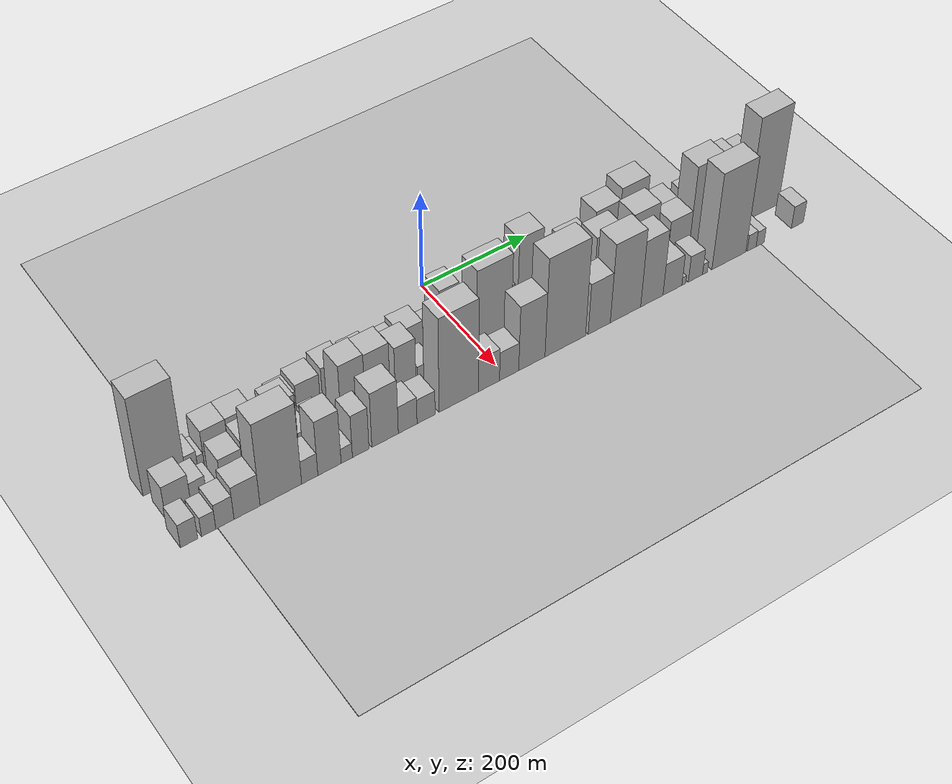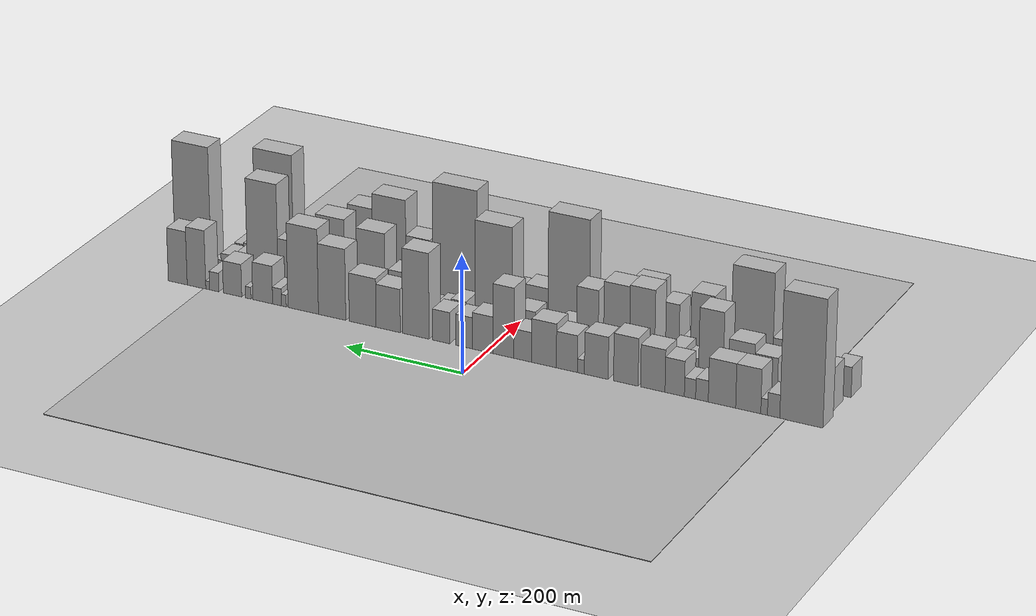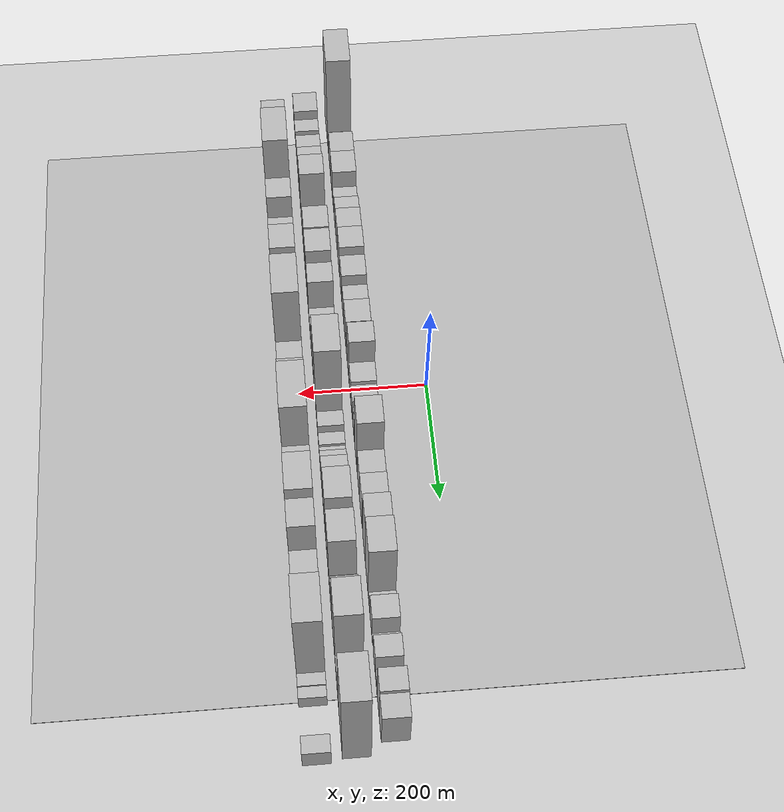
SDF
<?xml version="1.0" encoding="utf-8"?>

<sdf version="1.6">

   <world name="default">

      <gui fullscreen="0">

         <camera name="user_camera">

            <pose>-15 0 4.57585 0 0 0</pose>

            <view_controller>orbit</view_controller>

         </camera>

      </gui>

      <scene>

         <sky>

           <clouds>

             <speed>12</speed>

           </clouds>

         </sky>

         <ambient>0.4 0.4 0.4 1</ambient>

         <background>0.7 0.7 0.7 1</background>

         <shadows>1</shadows>

      </scene>

      <gravity>0 0 -9.8066</gravity>

      <magnetic_field>6e-06 2.3e-05 -4.2e-05</magnetic_field>

      <physics default="0" name="default_physics" type="ode">

         <ode>

            <solver>

               <type>quick</type>

               <iters>10</iters>

               <sor>1.0</sor>

               <use_dynamic_moi_rescaling>0</use_dynamic_moi_rescaling>

            </solver>

            <constraints>

               <cfm>0</cfm>

               <erp>0.2</erp>

               <contact_max_correcting_vel>100</contact_max_correcting_vel>

               <contact_surface_layer>0.001</contact_surface_layer>

            </constraints>

         </ode>

         <max_step_size>0.004</max_step_size>

         <real_time_factor>1</real_time_factor>

         <real_time_update_rate>250</real_time_update_rate>

      </physics>

      <light name="sun" type="directional">

         <cast_shadows>1</cast_shadows>

         <pose>0 0 10 0 0 0</pose>

         <diffuse>0.8 0.8 0.8 1</diffuse>

         <specular>0.2 0.2 0.2 1</specular>

         <attenuation>

            <range>1000</range>

            <constant>0.9</constant>

            <linear>0.01</linear>

            <quadratic>0.001</quadratic>

         </attenuation>

         <direction>-0.5 0.1 -0.9</direction>

      </light>

      <include>

         <name>ground_plane_1</name>

         <uri>model://HANNAS_ground_plane</uri>

         <pose>0 0 0  0 0 0</pose>

      </include>

      <include>

         <name>ground_plane_2</name>

         <uri>model://HANNAS_ground_plane</uri>

         <pose>100 0 0  0 0 0</pose>

      </include>

      <model name="building_1">

         <static>1</static>

         <pose frame="">100.0000 -525.1920 0 0.000000 0.000000 0.000000</pose>

         <link name="link">

            <pose frame="">0 0 106.50 0 0 0</pose>

            <collision name="collision">

               <geometry>

                  <box>

                     <size>40.0000 69.6161 213.0000</size>

                  </box>

               </geometry>

               <max_contacts>10</max_contacts>

               <surface>

                  <contact>

                     <ode/>

                  </contact>

                  <bounce/>

                  <friction>

                     <torsional>

                        <ode/>

                     </torsional>

                     <ode/>

                  </friction>

               </surface>

            </collision>

            <visual name="visual">

               <cast_shadows>0</cast_shadows>

               <geometry>

                  <box>

                     <size>40.0000 69.6161 213.0000</size>

                  </box>

               </geometry>

               <material>

                  <script>

                     <uri>model://HANNAS_wall/materials/scripts</uri>

                     <uri>model://HANNAS_wall/materials/textures</uri>

                     <name>vrc/HANNAS_wall</name>

                  </script>

               </material>

            </visual>

            <self_collide>0</self_collide>

            <enable_wind>0</enable_wind>

            <kinematic>0</kinematic>

         </link>

      </model>

      <model name="building_2">

         <static>1</static>

         <pose frame="">100.0000 -480.3971 0 0.000000 0.000000 0.000000</pose>

         <link name="link">

            <pose frame="">0 0 19.50 0 0 0</pose>

            <collision name="collision">

               <geometry>

                  <box>

                     <size>40.0000 19.9735 39.0000</size>

                  </box>

               </geometry>

               <max_contacts>10</max_contacts>

               <surface>

                  <contact>

                     <ode/>

                  </contact>

                  <bounce/>

                  <friction>

                     <torsional>

                        <ode/>

                     </torsional>

                     <ode/>

                  </friction>

               </surface>

            </collision>

            <visual name="visual">

               <cast_shadows>0</cast_shadows>

               <geometry>

                  <box>

                     <size>40.0000 19.9735 39.0000</size>

                  </box>

               </geometry>

               <material>

                  <script>

                     <uri>model://HANNAS_wall/materials/scripts</uri>

                     <uri>model://HANNAS_wall/materials/textures</uri>

                     <name>vrc/HANNAS_wall</name>

                  </script>

               </material>

            </visual>

            <self_collide>0</self_collide>

            <enable_wind>0</enable_wind>

            <kinematic>0</kinematic>

         </link>

      </model>

      <model name="building_3">

         <static>1</static>

         <pose frame="">100.0000 -464.9980 0 0.000000 0.000000 0.000000</pose>

         <link name="link">

            <pose frame="">0 0 13.50 0 0 0</pose>

            <collision name="collision">

               <geometry>

                  <box>

                     <size>40.0000 10.8247 27.0000</size>

                  </box>

               </geometry>

               <max_contacts>10</max_contacts>

               <surface>

                  <contact>

                     <ode/>

                  </contact>

                  <bounce/>

                  <friction>

                     <torsional>

                        <ode/>

                     </torsional>

                     <ode/>

                  </friction>

               </surface>

            </collision>

            <visual name="visual">

               <cast_shadows>0</cast_shadows>

               <geometry>

                  <box>

                     <size>40.0000 10.8247 27.0000</size>

                  </box>

               </geometry>

               <material>

                  <script>

                     <uri>model://HANNAS_wall/materials/scripts</uri>

                     <uri>model://HANNAS_wall/materials/textures</uri>

                     <name>vrc/HANNAS_wall</name>

                  </script>

               </material>

            </visual>

            <self_collide>0</self_collide>

            <enable_wind>0</enable_wind>

            <kinematic>0</kinematic>

         </link>

      </model>

      <model name="building_4">

         <static>1</static>

         <pose frame="">100.0000 -439.0959 0 0.000000 0.000000 0.000000</pose>

         <link name="link">

            <pose frame="">0 0 37.50 0 0 0</pose>

            <collision name="collision">

               <geometry>

                  <box>

                     <size>40.0000 40.9796 75.0000</size>

                  </box>

               </geometry>

               <max_contacts>10</max_contacts>

               <surface>

                  <contact>

                     <ode/>

                  </contact>

                  <bounce/>

                  <friction>

                     <torsional>

                        <ode/>

                     </torsional>

                     <ode/>

                  </friction>

               </surface>

            </collision>

            <visual name="visual">

               <cast_shadows>0</cast_shadows>

               <geometry>

                  <box>

                     <size>40.0000 40.9796 75.0000</size>

                  </box>

               </geometry>

               <material>

                  <script>

                     <uri>model://HANNAS_wall/materials/scripts</uri>

                     <uri>model://HANNAS_wall/materials/textures</uri>

                     <name>vrc/HANNAS_wall</name>

                  </script>

               </material>

            </visual>

            <self_collide>0</self_collide>

            <enable_wind>0</enable_wind>

            <kinematic>0</kinematic>

         </link>

      </model>

      <model name="building_5">

         <static>1</static>

         <pose frame="">100.0000 -396.1239 0 0.000000 0.000000 0.000000</pose>

         <link name="link">

            <pose frame="">0 0 37.50 0 0 0</pose>

            <collision name="collision">

               <geometry>

                  <box>

                     <size>40.0000 44.9645 75.0000</size>

                  </box>

               </geometry>

               <max_contacts>10</max_contacts>

               <surface>

                  <contact>

                     <ode/>

                  </contact>

                  <bounce/>

                  <friction>

                     <torsional>

                        <ode/>

                     </torsional>

                     <ode/>

                  </friction>

               </surface>

            </collision>

            <visual name="visual">

               <cast_shadows>0</cast_shadows>

               <geometry>

                  <box>

                     <size>40.0000 44.9645 75.0000</size>

                  </box>

               </geometry>

               <material>

                  <script>

                     <uri>model://HANNAS_wall/materials/scripts</uri>

                     <uri>model://HANNAS_wall/materials/textures</uri>

                     <name>vrc/HANNAS_wall</name>

                  </script>

               </material>

            </visual>

            <self_collide>0</self_collide>

            <enable_wind>0</enable_wind>

            <kinematic>0</kinematic>

         </link>

      </model>

      <model name="building_6">

         <static>1</static>

         <pose frame="">100.0000 -363.2750 0 0.000000 0.000000 0.000000</pose>

         <link name="link">

            <pose frame="">0 0 18.00 0 0 0</pose>

            <collision name="collision">

               <geometry>

                  <box>

                     <size>40.0000 20.7332 36.0000</size>

                  </box>

               </geometry>

               <max_contacts>10</max_contacts>

               <surface>

                  <contact>

                     <ode/>

                  </contact>

                  <bounce/>

                  <friction>

                     <torsional>

                        <ode/>

                     </torsional>

                     <ode/>

                  </friction>

               </surface>

            </collision>

            <visual name="visual">

               <cast_shadows>0</cast_shadows>

               <geometry>

                  <box>

                     <size>40.0000 20.7332 36.0000</size>

                  </box>

               </geometry>

               <material>

                  <script>

                     <uri>model://HANNAS_wall/materials/scripts</uri>

                     <uri>model://HANNAS_wall/materials/textures</uri>

                     <name>vrc/HANNAS_wall</name>

                  </script>

               </material>

            </visual>

            <self_collide>0</self_collide>

            <enable_wind>0</enable_wind>

            <kinematic>0</kinematic>

         </link>

      </model>

      <model name="building_7">

         <static>1</static>

         <pose frame="">100.0000 -343.6240 0 0.000000 0.000000 0.000000</pose>

         <link name="link">

            <pose frame="">0 0 16.50 0 0 0</pose>

            <collision name="collision">

               <geometry>

                  <box>

                     <size>40.0000 18.5687 33.0000</size>

                  </box>

               </geometry>

               <max_contacts>10</max_contacts>

               <surface>

                  <contact>

                     <ode/>

                  </contact>

                  <bounce/>

                  <friction>

                     <torsional>

                        <ode/>

                     </torsional>

                     <ode/>

                  </friction>

               </surface>

            </collision>

            <visual name="visual">

               <cast_shadows>0</cast_shadows>

               <geometry>

                  <box>

                     <size>40.0000 18.5687 33.0000</size>

                  </box>

               </geometry>

               <material>

                  <script>

                     <uri>model://HANNAS_wall/materials/scripts</uri>

                     <uri>model://HANNAS_wall/materials/textures</uri>

                     <name>vrc/HANNAS_wall</name>

                  </script>

               </material>

            </visual>

            <self_collide>0</self_collide>

            <enable_wind>0</enable_wind>

            <kinematic>0</kinematic>

         </link>

      </model>

      <model name="building_8">

         <static>1</static>

         <pose frame="">100.0000 -318.3260 0 0.000000 0.000000 0.000000</pose>

         <link name="link">

            <pose frame="">0 0 30.00 0 0 0</pose>

            <collision name="collision">

               <geometry>

                  <box>

                     <size>40.0000 32.0274 60.0000</size>

                  </box>

               </geometry>

               <max_contacts>10</max_contacts>

               <surface>

                  <contact>

                     <ode/>

                  </contact>

                  <bounce/>

                  <friction>

                     <torsional>

                        <ode/>

                     </torsional>

                     <ode/>

                  </friction>

               </surface>

            </collision>

            <visual name="visual">

               <cast_shadows>0</cast_shadows>

               <geometry>

                  <box>

                     <size>40.0000 32.0274 60.0000</size>

                  </box>

               </geometry>

               <material>

                  <script>

                     <uri>model://HANNAS_wall/materials/scripts</uri>

                     <uri>model://HANNAS_wall/materials/textures</uri>

                     <name>vrc/HANNAS_wall</name>

                  </script>

               </material>

            </visual>

            <self_collide>0</self_collide>

            <enable_wind>0</enable_wind>

            <kinematic>0</kinematic>

         </link>

      </model>

      <model name="building_9">

         <static>1</static>

         <pose frame="">100.0000 -281.9549 0 0.000000 0.000000 0.000000</pose>

         <link name="link">

            <pose frame="">0 0 36.00 0 0 0</pose>

            <collision name="collision">

               <geometry>

                  <box>

                     <size>40.0000 40.7148 72.0000</size>

                  </box>

               </geometry>

               <max_contacts>10</max_contacts>

               <surface>

                  <contact>

                     <ode/>

                  </contact>

                  <bounce/>

                  <friction>

                     <torsional>

                        <ode/>

                     </torsional>

                     <ode/>

                  </friction>

               </surface>

            </collision>

            <visual name="visual">

               <cast_shadows>0</cast_shadows>

               <geometry>

                  <box>

                     <size>40.0000 40.7148 72.0000</size>

                  </box>

               </geometry>

               <material>

                  <script>

                     <uri>model://HANNAS_wall/materials/scripts</uri>

                     <uri>model://HANNAS_wall/materials/textures</uri>

                     <name>vrc/HANNAS_wall</name>

                  </script>

               </material>

            </visual>

            <self_collide>0</self_collide>

            <enable_wind>0</enable_wind>

            <kinematic>0</kinematic>

         </link>

      </model>

      <model name="building_10">

         <static>1</static>

         <pose frame="">100.0000 -237.0497 0 0.000000 0.000000 0.000000</pose>

         <link name="link">

            <pose frame="">0 0 40.50 0 0 0</pose>

            <collision name="collision">

               <geometry>

                  <box>

                     <size>40.0000 41.0955 81.0000</size>

                  </box>

               </geometry>

               <max_contacts>10</max_contacts>

               <surface>

                  <contact>

                     <ode/>

                  </contact>

                  <bounce/>

                  <friction>

                     <torsional>

                        <ode/>

                     </torsional>

                     <ode/>

                  </friction>

               </surface>

            </collision>

            <visual name="visual">

               <cast_shadows>0</cast_shadows>

               <geometry>

                  <box>

                     <size>40.0000 41.0955 81.0000</size>

                  </box>

               </geometry>

               <material>

                  <script>

                     <uri>model://HANNAS_wall/materials/scripts</uri>

                     <uri>model://HANNAS_wall/materials/textures</uri>

                     <name>vrc/HANNAS_wall</name>

                  </script>

               </material>

            </visual>

            <self_collide>0</self_collide>

            <enable_wind>0</enable_wind>

            <kinematic>0</kinematic>

         </link>

      </model>

      <model name="building_11">

         <static>1</static>

         <pose frame="">100.0000 -187.5031 0 0.000000 0.000000 0.000000</pose>

         <link name="link">

            <pose frame="">0 0 36.00 0 0 0</pose>

            <collision name="collision">

               <geometry>

                  <box>

                     <size>40.0000 39.9978 72.0000</size>

                  </box>

               </geometry>

               <max_contacts>10</max_contacts>

               <surface>

                  <contact>

                     <ode/>

                  </contact>

                  <bounce/>

                  <friction>

                     <torsional>

                        <ode/>

                     </torsional>

                     <ode/>

                  </friction>

               </surface>

            </collision>

            <visual name="visual">

               <cast_shadows>0</cast_shadows>

               <geometry>

                  <box>

                     <size>40.0000 39.9978 72.0000</size>

                  </box>

               </geometry>

               <material>

                  <script>

                     <uri>model://HANNAS_wall/materials/scripts</uri>

                     <uri>model://HANNAS_wall/materials/textures</uri>

                     <name>vrc/HANNAS_wall</name>

                  </script>

               </material>

            </visual>

            <self_collide>0</self_collide>

            <enable_wind>0</enable_wind>

            <kinematic>0</kinematic>

         </link>

      </model>

      <model name="building_12">

         <static>1</static>

         <pose frame="">100.0000 -161.5487 0 0.000000 0.000000 0.000000</pose>

         <link name="link">

            <pose frame="">0 0 12.00 0 0 0</pose>

            <collision name="collision">

               <geometry>

                  <box>

                     <size>40.0000 11.9110 24.0000</size>

                  </box>

               </geometry>

               <max_contacts>10</max_contacts>

               <surface>

                  <contact>

                     <ode/>

                  </contact>

                  <bounce/>

                  <friction>

                     <torsional>

                        <ode/>

                     </torsional>

                     <ode/>

                  </friction>

               </surface>

            </collision>

            <visual name="visual">

               <cast_shadows>0</cast_shadows>

               <geometry>

                  <box>

                     <size>40.0000 11.9110 24.0000</size>

                  </box>

               </geometry>

               <material>

                  <script>

                     <uri>model://HANNAS_wall/materials/scripts</uri>

                     <uri>model://HANNAS_wall/materials/textures</uri>

                     <name>vrc/HANNAS_wall</name>

                  </script>

               </material>

            </visual>

            <self_collide>0</self_collide>

            <enable_wind>0</enable_wind>

            <kinematic>0</kinematic>

         </link>

      </model>

      <model name="building_13">

         <static>1</static>

         <pose frame="">100.0000 -137.8697 0 0.000000 0.000000 0.000000</pose>

         <link name="link">

            <pose frame="">0 0 31.50 0 0 0</pose>

            <collision name="collision">

               <geometry>

                  <box>

                     <size>40.0000 35.4469 63.0000</size>

                  </box>

               </geometry>

               <max_contacts>10</max_contacts>

               <surface>

                  <contact>

                     <ode/>

                  </contact>

                  <bounce/>

                  <friction>

                     <torsional>

                        <ode/>

                     </torsional>

                     <ode/>

                  </friction>

               </surface>

            </collision>

            <visual name="visual">

               <cast_shadows>0</cast_shadows>

               <geometry>

                  <box>

                     <size>40.0000 35.4469 63.0000</size>

                  </box>

               </geometry>

               <material>

                  <script>

                     <uri>model://HANNAS_wall/materials/scripts</uri>

                     <uri>model://HANNAS_wall/materials/textures</uri>

                     <name>vrc/HANNAS_wall</name>

                  </script>

               </material>

            </visual>

            <self_collide>0</self_collide>

            <enable_wind>0</enable_wind>

            <kinematic>0</kinematic>

         </link>

      </model>

      <model name="building_14">

         <static>1</static>

         <pose frame="">100.0000 -99.2202 0 0.000000 0.000000 0.000000</pose>

         <link name="link">

            <pose frame="">0 0 37.50 0 0 0</pose>

            <collision name="collision">

               <geometry>

                  <box>

                     <size>40.0000 41.8522 75.0000</size>

                  </box>

               </geometry>

               <max_contacts>10</max_contacts>

               <surface>

                  <contact>

                     <ode/>

                  </contact>

                  <bounce/>

                  <friction>

                     <torsional>

                        <ode/>

                     </torsional>

                     <ode/>

                  </friction>

               </surface>

            </collision>

            <visual name="visual">

               <cast_shadows>0</cast_shadows>

               <geometry>

                  <box>

                     <size>40.0000 41.8522 75.0000</size>

                  </box>

               </geometry>

               <material>

                  <script>

                     <uri>model://HANNAS_wall/materials/scripts</uri>

                     <uri>model://HANNAS_wall/materials/textures</uri>

                     <name>vrc/HANNAS_wall</name>

                  </script>

               </material>

            </visual>

            <self_collide>0</self_collide>

            <enable_wind>0</enable_wind>

            <kinematic>0</kinematic>

         </link>

      </model>

      <model name="building_15">

         <static>1</static>

         <pose frame="">100.0000 -63.1004 0 0.000000 0.000000 0.000000</pose>

         <link name="link">

            <pose frame="">0 0 25.50 0 0 0</pose>

            <collision name="collision">

               <geometry>

                  <box>

                     <size>40.0000 30.3875 51.0000</size>

                  </box>

               </geometry>

               <max_contacts>10</max_contacts>

               <surface>

                  <contact>

                     <ode/>

                  </contact>

                  <bounce/>

                  <friction>

                     <torsional>

                        <ode/>

                     </torsional>

                     <ode/>

                  </friction>

               </surface>

            </collision>

            <visual name="visual">

               <cast_shadows>0</cast_shadows>

               <geometry>

                  <box>

                     <size>40.0000 30.3875 51.0000</size>

                  </box>

               </geometry>

               <material>

                  <script>

                     <uri>model://HANNAS_wall/materials/scripts</uri>

                     <uri>model://HANNAS_wall/materials/textures</uri>

                     <name>vrc/HANNAS_wall</name>

                  </script>

               </material>

            </visual>

            <self_collide>0</self_collide>

            <enable_wind>0</enable_wind>

            <kinematic>0</kinematic>

         </link>

      </model>

      <model name="building_16">

         <static>1</static>

         <pose frame="">100.0000 -29.7514 0 0.000000 0.000000 0.000000</pose>

         <link name="link">

            <pose frame="">0 0 60.00 0 0 0</pose>

            <collision name="collision">

               <geometry>

                  <box>

                     <size>40.0000 36.3105 120.0000</size>

                  </box>

               </geometry>

               <max_contacts>10</max_contacts>

               <surface>

                  <contact>

                     <ode/>

                  </contact>

                  <bounce/>

                  <friction>

                     <torsional>

                        <ode/>

                     </torsional>

                     <ode/>

                  </friction>

               </surface>

            </collision>

            <visual name="visual">

               <cast_shadows>0</cast_shadows>

               <geometry>

                  <box>

                     <size>40.0000 36.3105 120.0000</size>

                  </box>

               </geometry>

               <material>

                  <script>

                     <uri>model://HANNAS_wall/materials/scripts</uri>

                     <uri>model://HANNAS_wall/materials/textures</uri>

                     <name>vrc/HANNAS_wall</name>

                  </script>

               </material>

            </visual>

            <self_collide>0</self_collide>

            <enable_wind>0</enable_wind>

            <kinematic>0</kinematic>

         </link>

      </model>

      <model name="building_17">

         <static>1</static>

         <pose frame="">100.0000 5.9926 0 0.000000 0.000000 0.000000</pose>

         <link name="link">

            <pose frame="">0 0 31.50 0 0 0</pose>

            <collision name="collision">

               <geometry>

                  <box>

                     <size>40.0000 35.1775 63.0000</size>

                  </box>

               </geometry>

               <max_contacts>10</max_contacts>

               <surface>

                  <contact>

                     <ode/>

                  </contact>

                  <bounce/>

                  <friction>

                     <torsional>

                        <ode/>

                     </torsional>

                     <ode/>

                  </friction>

               </surface>

            </collision>

            <visual name="visual">

               <cast_shadows>0</cast_shadows>

               <geometry>

                  <box>

                     <size>40.0000 35.1775 63.0000</size>

                  </box>

               </geometry>

               <material>

                  <script>

                     <uri>model://HANNAS_wall/materials/scripts</uri>

                     <uri>model://HANNAS_wall/materials/textures</uri>

                     <name>vrc/HANNAS_wall</name>

                  </script>

               </material>

            </visual>

            <self_collide>0</self_collide>

            <enable_wind>0</enable_wind>

            <kinematic>0</kinematic>

         </link>

      </model>

      <model name="building_18">

         <static>1</static>

         <pose frame="">100.0000 38.0278 0 0.000000 0.000000 0.000000</pose>

         <link name="link">

            <pose frame="">0 0 27.00 0 0 0</pose>

            <collision name="collision">

               <geometry>

                  <box>

                     <size>40.0000 28.8929 54.0000</size>

                  </box>

               </geometry>

               <max_contacts>10</max_contacts>

               <surface>

                  <contact>

                     <ode/>

                  </contact>

                  <bounce/>

                  <friction>

                     <torsional>

                        <ode/>

                     </torsional>

                     <ode/>

                  </friction>

               </surface>

            </collision>

            <visual name="visual">

               <cast_shadows>0</cast_shadows>

               <geometry>

                  <box>

                     <size>40.0000 28.8929 54.0000</size>

                  </box>

               </geometry>

               <material>

                  <script>

                     <uri>model://HANNAS_wall/materials/scripts</uri>

                     <uri>model://HANNAS_wall/materials/textures</uri>

                     <name>vrc/HANNAS_wall</name>

                  </script>

               </material>

            </visual>

            <self_collide>0</self_collide>

            <enable_wind>0</enable_wind>

            <kinematic>0</kinematic>

         </link>

      </model>

      <model name="building_19">

         <static>1</static>

         <pose frame="">100.0000 77.4968 0 0.000000 0.000000 0.000000</pose>

         <link name="link">

            <pose frame="">0 0 27.00 0 0 0</pose>

            <collision name="collision">

               <geometry>

                  <box>

                     <size>40.0000 30.0453 54.0000</size>

                  </box>

               </geometry>

               <max_contacts>10</max_contacts>

               <surface>

                  <contact>

                     <ode/>

                  </contact>

                  <bounce/>

                  <friction>

                     <torsional>

                        <ode/>

                     </torsional>

                     <ode/>

                  </friction>

               </surface>

            </collision>

            <visual name="visual">

               <cast_shadows>0</cast_shadows>

               <geometry>

                  <box>

                     <size>40.0000 30.0453 54.0000</size>

                  </box>

               </geometry>

               <material>

                  <script>

                     <uri>model://HANNAS_wall/materials/scripts</uri>

                     <uri>model://HANNAS_wall/materials/textures</uri>

                     <name>vrc/HANNAS_wall</name>

                  </script>

               </material>

            </visual>

            <self_collide>0</self_collide>

            <enable_wind>0</enable_wind>

            <kinematic>0</kinematic>

         </link>

      </model>

      <model name="building_20">

         <static>1</static>

         <pose frame="">100.0000 121.6650 0 0.000000 0.000000 0.000000</pose>

         <link name="link">

            <pose frame="">0 0 73.50 0 0 0</pose>

            <collision name="collision">

               <geometry>

                  <box>

                     <size>40.0000 46.2910 147.0000</size>

                  </box>

               </geometry>

               <max_contacts>10</max_contacts>

               <surface>

                  <contact>

                     <ode/>

                  </contact>

                  <bounce/>

                  <friction>

                     <torsional>

                        <ode/>

                     </torsional>

                     <ode/>

                  </friction>

               </surface>

            </collision>

            <visual name="visual">

               <cast_shadows>0</cast_shadows>

               <geometry>

                  <box>

                     <size>40.0000 46.2910 147.0000</size>

                  </box>

               </geometry>

               <material>

                  <script>

                     <uri>model://HANNAS_wall/materials/scripts</uri>

                     <uri>model://HANNAS_wall/materials/textures</uri>

                     <name>vrc/HANNAS_wall</name>

                  </script>

               </material>

            </visual>

            <self_collide>0</self_collide>

            <enable_wind>0</enable_wind>

            <kinematic>0</kinematic>

         </link>

      </model>

      <model name="building_21">

         <static>1</static>

         <pose frame="">100.0000 170.0581 0 0.000000 0.000000 0.000000</pose>

         <link name="link">

            <pose frame="">0 0 37.50 0 0 0</pose>

            <collision name="collision">

               <geometry>

                  <box>

                     <size>40.0000 42.4953 75.0000</size>

                  </box>

               </geometry>

               <max_contacts>10</max_contacts>

               <surface>

                  <contact>

                     <ode/>

                  </contact>

                  <bounce/>

                  <friction>

                     <torsional>

                        <ode/>

                     </torsional>

                     <ode/>

                  </friction>

               </surface>

            </collision>

            <visual name="visual">

               <cast_shadows>0</cast_shadows>

               <geometry>

                  <box>

                     <size>40.0000 42.4953 75.0000</size>

                  </box>

               </geometry>

               <material>

                  <script>

                     <uri>model://HANNAS_wall/materials/scripts</uri>

                     <uri>model://HANNAS_wall/materials/textures</uri>

                     <name>vrc/HANNAS_wall</name>

                  </script>

               </material>

            </visual>

            <self_collide>0</self_collide>

            <enable_wind>0</enable_wind>

            <kinematic>0</kinematic>

         </link>

      </model>

      <model name="building_22">

         <static>1</static>

         <pose frame="">100.0000 215.0533 0 0.000000 0.000000 0.000000</pose>

         <link name="link">

            <pose frame="">0 0 42.00 0 0 0</pose>

            <collision name="collision">

               <geometry>

                  <box>

                     <size>40.0000 47.4951 84.0000</size>

                  </box>

               </geometry>

               <max_contacts>10</max_contacts>

               <surface>

                  <contact>

                     <ode/>

                  </contact>

                  <bounce/>

                  <friction>

                     <torsional>

                        <ode/>

                     </torsional>

                     <ode/>

                  </friction>

               </surface>

            </collision>

            <visual name="visual">

               <cast_shadows>0</cast_shadows>

               <geometry>

                  <box>

                     <size>40.0000 47.4951 84.0000</size>

                  </box>

               </geometry>

               <material>

                  <script>

                     <uri>model://HANNAS_wall/materials/scripts</uri>

                     <uri>model://HANNAS_wall/materials/textures</uri>

                     <name>vrc/HANNAS_wall</name>

                  </script>

               </material>

            </visual>

            <self_collide>0</self_collide>

            <enable_wind>0</enable_wind>

            <kinematic>0</kinematic>

         </link>

      </model>

      <model name="building_23">

         <static>1</static>

         <pose frame="">100.0000 269.0989 0 0.000000 0.000000 0.000000</pose>

         <link name="link">

            <pose frame="">0 0 61.50 0 0 0</pose>

            <collision name="collision">

               <geometry>

                  <box>

                     <size>40.0000 48.5960 123.0000</size>

                  </box>

               </geometry>

               <max_contacts>10</max_contacts>

               <surface>

                  <contact>

                     <ode/>

                  </contact>

                  <bounce/>

                  <friction>

                     <torsional>

                        <ode/>

                     </torsional>

                     <ode/>

                  </friction>

               </surface>

            </collision>

            <visual name="visual">

               <cast_shadows>0</cast_shadows>

               <geometry>

                  <box>

                     <size>40.0000 48.5960 123.0000</size>

                  </box>

               </geometry>

               <material>

                  <script>

                     <uri>model://HANNAS_wall/materials/scripts</uri>

                     <uri>model://HANNAS_wall/materials/textures</uri>

                     <name>vrc/HANNAS_wall</name>

                  </script>

               </material>

            </visual>

            <self_collide>0</self_collide>

            <enable_wind>0</enable_wind>

            <kinematic>0</kinematic>

         </link>

      </model>

      <model name="building_24">

         <static>1</static>

         <pose frame="">100.0000 320.6359 0 0.000000 0.000000 0.000000</pose>

         <link name="link">

            <pose frame="">0 0 73.50 0 0 0</pose>

            <collision name="collision">

               <geometry>

                  <box>

                     <size>40.0000 54.4780 147.0000</size>

                  </box>

               </geometry>

               <max_contacts>10</max_contacts>

               <surface>

                  <contact>

                     <ode/>

                  </contact>

                  <bounce/>

                  <friction>

                     <torsional>

                        <ode/>

                     </torsional>

                     <ode/>

                  </friction>

               </surface>

            </collision>

            <visual name="visual">

               <cast_shadows>0</cast_shadows>

               <geometry>

                  <box>

                     <size>40.0000 54.4780 147.0000</size>

                  </box>

               </geometry>

               <material>

                  <script>

                     <uri>model://HANNAS_wall/materials/scripts</uri>

                     <uri>model://HANNAS_wall/materials/textures</uri>

                     <name>vrc/HANNAS_wall</name>

                  </script>

               </material>

            </visual>

            <self_collide>0</self_collide>

            <enable_wind>0</enable_wind>

            <kinematic>0</kinematic>

         </link>

      </model>

      <model name="building_25">

         <static>1</static>

         <pose frame="">100.0000 355.2845 0 0.000000 0.000000 0.000000</pose>

         <link name="link">

            <pose frame="">0 0 10.50 0 0 0</pose>

            <collision name="collision">

               <geometry>

                  <box>

                     <size>40.0000 8.8193 21.0000</size>

                  </box>

               </geometry>

               <max_contacts>10</max_contacts>

               <surface>

                  <contact>

                     <ode/>

                  </contact>

                  <bounce/>

                  <friction>

                     <torsional>

                        <ode/>

                     </torsional>

                     <ode/>

                  </friction>

               </surface>

            </collision>

            <visual name="visual">

               <cast_shadows>0</cast_shadows>

               <geometry>

                  <box>

                     <size>40.0000 8.8193 21.0000</size>

                  </box>

               </geometry>

               <material>

                  <script>

                     <uri>model://HANNAS_wall/materials/scripts</uri>

                     <uri>model://HANNAS_wall/materials/textures</uri>

                     <name>vrc/HANNAS_wall</name>

                  </script>

               </material>

            </visual>

            <self_collide>0</self_collide>

            <enable_wind>0</enable_wind>

            <kinematic>0</kinematic>

         </link>

      </model>

      <model name="building_26">

         <static>1</static>

         <pose frame="">100.0000 367.5950 0 0.000000 0.000000 0.000000</pose>

         <link name="link">

            <pose frame="">0 0 15.00 0 0 0</pose>

            <collision name="collision">

               <geometry>

                  <box>

                     <size>40.0000 15.8017 30.0000</size>

                  </box>

               </geometry>

               <max_contacts>10</max_contacts>

               <surface>

                  <contact>

                     <ode/>

                  </contact>

                  <bounce/>

                  <friction>

                     <torsional>

                        <ode/>

                     </torsional>

                     <ode/>

                  </friction>

               </surface>

            </collision>

            <visual name="visual">

               <cast_shadows>0</cast_shadows>

               <geometry>

                  <box>

                     <size>40.0000 15.8017 30.0000</size>

                  </box>

               </geometry>

               <material>

                  <script>

                     <uri>model://HANNAS_wall/materials/scripts</uri>

                     <uri>model://HANNAS_wall/materials/textures</uri>

                     <name>vrc/HANNAS_wall</name>

                  </script>

               </material>

            </visual>

            <self_collide>0</self_collide>

            <enable_wind>0</enable_wind>

            <kinematic>0</kinematic>

         </link>

      </model>

      <model name="building_27">

         <static>1</static>

         <pose frame="">100.0000 393.4239 0 0.000000 0.000000 0.000000</pose>

         <link name="link">

            <pose frame="">0 0 33.00 0 0 0</pose>

            <collision name="collision">

               <geometry>

                  <box>

                     <size>40.0000 35.8562 66.0000</size>

                  </box>

               </geometry>

               <max_contacts>10</max_contacts>

               <surface>

                  <contact>

                     <ode/>

                  </contact>

                  <bounce/>

                  <friction>

                     <torsional>

                        <ode/>

                     </torsional>

                     <ode/>

                  </friction>

               </surface>

            </collision>

            <visual name="visual">

               <cast_shadows>0</cast_shadows>

               <geometry>

                  <box>

                     <size>40.0000 35.8562 66.0000</size>

                  </box>

               </geometry>

               <material>

                  <script>

                     <uri>model://HANNAS_wall/materials/scripts</uri>

                     <uri>model://HANNAS_wall/materials/textures</uri>

                     <name>vrc/HANNAS_wall</name>

                  </script>

               </material>

            </visual>

            <self_collide>0</self_collide>

            <enable_wind>0</enable_wind>

            <kinematic>0</kinematic>

         </link>

      </model>

      <model name="building_28">

         <static>1</static>

         <pose frame="">100.0000 419.2953 0 0.000000 0.000000 0.000000</pose>

         <link name="link">

            <pose frame="">0 0 10.50 0 0 0</pose>

            <collision name="collision">

               <geometry>

                  <box>

                     <size>40.0000 9.8866 21.0000</size>

                  </box>

               </geometry>

               <max_contacts>10</max_contacts>

               <surface>

                  <contact>

                     <ode/>

                  </contact>

                  <bounce/>

                  <friction>

                     <torsional>

                        <ode/>

                     </torsional>

                     <ode/>

                  </friction>

               </surface>

            </collision>

            <visual name="visual">

               <cast_shadows>0</cast_shadows>

               <geometry>

                  <box>

                     <size>40.0000 9.8866 21.0000</size>

                  </box>

               </geometry>

               <material>

                  <script>

                     <uri>model://HANNAS_wall/materials/scripts</uri>

                     <uri>model://HANNAS_wall/materials/textures</uri>

                     <name>vrc/HANNAS_wall</name>

                  </script>

               </material>

            </visual>

            <self_collide>0</self_collide>

            <enable_wind>0</enable_wind>

            <kinematic>0</kinematic>

         </link>

      </model>

      <model name="building_29">

         <static>1</static>

         <pose frame="">100.0000 447.9776 0 0.000000 0.000000 0.000000</pose>

         <link name="link">

            <pose frame="">0 0 28.50 0 0 0</pose>

            <collision name="collision">

               <geometry>

                  <box>

                     <size>40.0000 33.4781 57.0000</size>

                  </box>

               </geometry>

               <max_contacts>10</max_contacts>

               <surface>

                  <contact>

                     <ode/>

                  </contact>

                  <bounce/>

                  <friction>

                     <torsional>

                        <ode/>

                     </torsional>

                     <ode/>

                  </friction>

               </surface>

            </collision>

            <visual name="visual">

               <cast_shadows>0</cast_shadows>

               <geometry>

                  <box>

                     <size>40.0000 33.4781 57.0000</size>

                  </box>

               </geometry>

               <material>

                  <script>

                     <uri>model://HANNAS_wall/materials/scripts</uri>

                     <uri>model://HANNAS_wall/materials/textures</uri>

                     <name>vrc/HANNAS_wall</name>

                  </script>

               </material>

            </visual>

            <self_collide>0</self_collide>

            <enable_wind>0</enable_wind>

            <kinematic>0</kinematic>

         </link>

      </model>

      <model name="building_30">

         <static>1</static>

         <pose frame="">100.0000 481.2106 0 0.000000 0.000000 0.000000</pose>

         <link name="link">

            <pose frame="">0 0 16.50 0 0 0</pose>

            <collision name="collision">

               <geometry>

                  <box>

                     <size>40.0000 16.9878 33.0000</size>

                  </box>

               </geometry>

               <max_contacts>10</max_contacts>

               <surface>

                  <contact>

                     <ode/>

                  </contact>

                  <bounce/>

                  <friction>

                     <torsional>

                        <ode/>

                     </torsional>

                     <ode/>

                  </friction>

               </surface>

            </collision>

            <visual name="visual">

               <cast_shadows>0</cast_shadows>

               <geometry>

                  <box>

                     <size>40.0000 16.9878 33.0000</size>

                  </box>

               </geometry>

               <material>

                  <script>

                     <uri>model://HANNAS_wall/materials/scripts</uri>

                     <uri>model://HANNAS_wall/materials/textures</uri>

                     <name>vrc/HANNAS_wall</name>

                  </script>

               </material>

            </visual>

            <self_collide>0</self_collide>

            <enable_wind>0</enable_wind>

            <kinematic>0</kinematic>

         </link>

      </model>

      <model name="building_31">

         <static>1</static>

         <pose frame="">100.0000 493.1604 0 0.000000 0.000000 0.000000</pose>

         <link name="link">

            <pose frame="">0 0 7.50 0 0 0</pose>

            <collision name="collision">

               <geometry>

                  <box>

                     <size>40.0000 6.9120 15.0000</size>

                  </box>

               </geometry>

               <max_contacts>10</max_contacts>

               <surface>

                  <contact>

                     <ode/>

                  </contact>

                  <bounce/>

                  <friction>

                     <torsional>

                        <ode/>

                     </torsional>

                     <ode/>

                  </friction>

               </surface>

            </collision>

            <visual name="visual">

               <cast_shadows>0</cast_shadows>

               <geometry>

                  <box>

                     <size>40.0000 6.9120 15.0000</size>

                  </box>

               </geometry>

               <material>

                  <script>

                     <uri>model://HANNAS_wall/materials/scripts</uri>

                     <uri>model://HANNAS_wall/materials/textures</uri>

                     <name>vrc/HANNAS_wall</name>

                  </script>

               </material>

            </visual>

            <self_collide>0</self_collide>

            <enable_wind>0</enable_wind>

            <kinematic>0</kinematic>

         </link>

      </model>

      <model name="building_32">

         <static>1</static>

         <pose frame="">100.0000 513.6089 0 0.000000 0.000000 0.000000</pose>

         <link name="link">

            <pose frame="">0 0 51.00 0 0 0</pose>

            <collision name="collision">

               <geometry>

                  <box>

                     <size>40.0000 33.9849 102.0000</size>

                  </box>

               </geometry>

               <max_contacts>10</max_contacts>

               <surface>

                  <contact>

                     <ode/>

                  </contact>

                  <bounce/>

                  <friction>

                     <torsional>

                        <ode/>

                     </torsional>

                     <ode/>

                  </friction>

               </surface>

            </collision>

            <visual name="visual">

               <cast_shadows>0</cast_shadows>

               <geometry>

                  <box>

                     <size>40.0000 33.9849 102.0000</size>

                  </box>

               </geometry>

               <material>

                  <script>

                     <uri>model://HANNAS_wall/materials/scripts</uri>

                     <uri>model://HANNAS_wall/materials/textures</uri>

                     <name>vrc/HANNAS_wall</name>

                  </script>

               </material>

            </visual>

            <self_collide>0</self_collide>

            <enable_wind>0</enable_wind>

            <kinematic>0</kinematic>

         </link>

      </model>

      <model name="building_33">

         <static>1</static>

         <pose frame="">100.0000 547.9247 0 0.000000 0.000000 0.000000</pose>

         <link name="link">

            <pose frame="">0 0 46.50 0 0 0</pose>

            <collision name="collision">

               <geometry>

                  <box>

                     <size>40.0000 34.6466 93.0000</size>

                  </box>

               </geometry>

               <max_contacts>10</max_contacts>

               <surface>

                  <contact>

                     <ode/>

                  </contact>

                  <bounce/>

                  <friction>

                     <torsional>

                        <ode/>

                     </torsional>

                     <ode/>

                  </friction>

               </surface>

            </collision>

            <visual name="visual">

               <cast_shadows>0</cast_shadows>

               <geometry>

                  <box>

                     <size>40.0000 34.6466 93.0000</size>

                  </box>

               </geometry>

               <material>

                  <script>

                     <uri>model://HANNAS_wall/materials/scripts</uri>

                     <uri>model://HANNAS_wall/materials/textures</uri>

                     <name>vrc/HANNAS_wall</name>

                  </script>

               </material>

            </visual>

            <self_collide>0</self_collide>

            <enable_wind>0</enable_wind>

            <kinematic>0</kinematic>

         </link>

      </model>

      <model name="building_34">

         <static>1</static>

         <pose frame="">155.0000 -532.4079 0 0.000000 0.000000 0.000000</pose>

         <link name="link">

            <pose frame="">0 0 36.00 0 0 0</pose>

            <collision name="collision">

               <geometry>

                  <box>

                     <size>40.0000 41.1843 72.0000</size>

                  </box>

               </geometry>

               <max_contacts>10</max_contacts>

               <surface>

                  <contact>

                     <ode/>

                  </contact>

                  <bounce/>

                  <friction>

                     <torsional>

                        <ode/>

                     </torsional>

                     <ode/>

                  </friction>

               </surface>

            </collision>

            <visual name="visual">

               <cast_shadows>0</cast_shadows>

               <geometry>

                  <box>

                     <size>40.0000 41.1843 72.0000</size>

                  </box>

               </geometry>

               <material>

                  <script>

                     <uri>model://HANNAS_wall/materials/scripts</uri>

                     <uri>model://HANNAS_wall/materials/textures</uri>

                     <name>vrc/HANNAS_wall</name>

                  </script>

               </material>

            </visual>

            <self_collide>0</self_collide>

            <enable_wind>0</enable_wind>

            <kinematic>0</kinematic>

         </link>

      </model>

      <model name="building_35">

         <static>1</static>

         <pose frame="">155.0000 -498.9402 0 0.000000 0.000000 0.000000</pose>

         <link name="link">

            <pose frame="">0 0 25.50 0 0 0</pose>

            <collision name="collision">

               <geometry>

                  <box>

                     <size>40.0000 25.7511 51.0000</size>

                  </box>

               </geometry>

               <max_contacts>10</max_contacts>

               <surface>

                  <contact>

                     <ode/>

                  </contact>

                  <bounce/>

                  <friction>

                     <torsional>

                        <ode/>

                     </torsional>

                     <ode/>

                  </friction>

               </surface>

            </collision>

            <visual name="visual">

               <cast_shadows>0</cast_shadows>

               <geometry>

                  <box>

                     <size>40.0000 25.7511 51.0000</size>

                  </box>

               </geometry>

               <material>

                  <script>

                     <uri>model://HANNAS_wall/materials/scripts</uri>

                     <uri>model://HANNAS_wall/materials/textures</uri>

                     <name>vrc/HANNAS_wall</name>

                  </script>

               </material>

            </visual>

            <self_collide>0</self_collide>

            <enable_wind>0</enable_wind>

            <kinematic>0</kinematic>

         </link>

      </model>

      <model name="building_36">

         <static>1</static>

         <pose frame="">155.0000 -477.3509 0 0.000000 0.000000 0.000000</pose>

         <link name="link">

            <pose frame="">0 0 15.00 0 0 0</pose>

            <collision name="collision">

               <geometry>

                  <box>

                     <size>40.0000 17.4274 30.0000</size>

                  </box>

               </geometry>

               <max_contacts>10</max_contacts>

               <surface>

                  <contact>

                     <ode/>

                  </contact>

                  <bounce/>

                  <friction>

                     <torsional>

                        <ode/>

                     </torsional>

                     <ode/>

                  </friction>

               </surface>

            </collision>

            <visual name="visual">

               <cast_shadows>0</cast_shadows>

               <geometry>

                  <box>

                     <size>40.0000 17.4274 30.0000</size>

                  </box>

               </geometry>

               <material>

                  <script>

                     <uri>model://HANNAS_wall/materials/scripts</uri>

                     <uri>model://HANNAS_wall/materials/textures</uri>

                     <name>vrc/HANNAS_wall</name>

                  </script>

               </material>

            </visual>

            <self_collide>0</self_collide>

            <enable_wind>0</enable_wind>

            <kinematic>0</kinematic>

         </link>

      </model>

      <model name="building_37">

         <static>1</static>

         <pose frame="">155.0000 -443.7646 0 0.000000 0.000000 0.000000</pose>

         <link name="link">

            <pose frame="">0 0 34.50 0 0 0</pose>

            <collision name="collision">

               <geometry>

                  <box>

                     <size>40.0000 37.7451 69.0000</size>

                  </box>

               </geometry>

               <max_contacts>10</max_contacts>

               <surface>

                  <contact>

                     <ode/>

                  </contact>

                  <bounce/>

                  <friction>

                     <torsional>

                        <ode/>

                     </torsional>

                     <ode/>

                  </friction>

               </surface>

            </collision>

            <visual name="visual">

               <cast_shadows>0</cast_shadows>

               <geometry>

                  <box>

                     <size>40.0000 37.7451 69.0000</size>

                  </box>

               </geometry>

               <material>

                  <script>

                     <uri>model://HANNAS_wall/materials/scripts</uri>

                     <uri>model://HANNAS_wall/materials/textures</uri>

                     <name>vrc/HANNAS_wall</name>

                  </script>

               </material>

            </visual>

            <self_collide>0</self_collide>

            <enable_wind>0</enable_wind>

            <kinematic>0</kinematic>

         </link>

      </model>

      <model name="building_38">

         <static>1</static>

         <pose frame="">155.0000 -403.7173 0 0.000000 0.000000 0.000000</pose>

         <link name="link">

            <pose frame="">0 0 42.00 0 0 0</pose>

            <collision name="collision">

               <geometry>

                  <box>

                     <size>40.0000 42.3496 84.0000</size>

                  </box>

               </geometry>

               <max_contacts>10</max_contacts>

               <surface>

                  <contact>

                     <ode/>

                  </contact>

                  <bounce/>

                  <friction>

                     <torsional>

                        <ode/>

                     </torsional>

                     <ode/>

                  </friction>

               </surface>

            </collision>

            <visual name="visual">

               <cast_shadows>0</cast_shadows>

               <geometry>

                  <box>

                     <size>40.0000 42.3496 84.0000</size>

                  </box>

               </geometry>

               <material>

                  <script>

                     <uri>model://HANNAS_wall/materials/scripts</uri>

                     <uri>model://HANNAS_wall/materials/textures</uri>

                     <name>vrc/HANNAS_wall</name>

                  </script>

               </material>

            </visual>

            <self_collide>0</self_collide>

            <enable_wind>0</enable_wind>

            <kinematic>0</kinematic>

         </link>

      </model>

      <model name="building_39">

         <static>1</static>

         <pose frame="">155.0000 -353.1470 0 0.000000 0.000000 0.000000</pose>

         <link name="link">

            <pose frame="">0 0 63.00 0 0 0</pose>

            <collision name="collision">

               <geometry>

                  <box>

                     <size>40.0000 40.7909 126.0000</size>

                  </box>

               </geometry>

               <max_contacts>10</max_contacts>

               <surface>

                  <contact>

                     <ode/>

                  </contact>

                  <bounce/>

                  <friction>

                     <torsional>

                        <ode/>

                     </torsional>

                     <ode/>

                  </friction>

               </surface>

            </collision>

            <visual name="visual">

               <cast_shadows>0</cast_shadows>

               <geometry>

                  <box>

                     <size>40.0000 40.7909 126.0000</size>

                  </box>

               </geometry>

               <material>

                  <script>

                     <uri>model://HANNAS_wall/materials/scripts</uri>

                     <uri>model://HANNAS_wall/materials/textures</uri>

                     <name>vrc/HANNAS_wall</name>

                  </script>

               </material>

            </visual>

            <self_collide>0</self_collide>

            <enable_wind>0</enable_wind>

            <kinematic>0</kinematic>

         </link>

      </model>

      <model name="building_40">

         <static>1</static>

         <pose frame="">155.0000 -321.5371 0 0.000000 0.000000 0.000000</pose>

         <link name="link">

            <pose frame="">0 0 19.50 0 0 0</pose>

            <collision name="collision">

               <geometry>

                  <box>

                     <size>40.0000 22.4290 39.0000</size>

                  </box>

               </geometry>

               <max_contacts>10</max_contacts>

               <surface>

                  <contact>

                     <ode/>

                  </contact>

                  <bounce/>

                  <friction>

                     <torsional>

                        <ode/>

                     </torsional>

                     <ode/>

                  </friction>

               </surface>

            </collision>

            <visual name="visual">

               <cast_shadows>0</cast_shadows>

               <geometry>

                  <box>

                     <size>40.0000 22.4290 39.0000</size>

                  </box>

               </geometry>

               <material>

                  <script>

                     <uri>model://HANNAS_wall/materials/scripts</uri>

                     <uri>model://HANNAS_wall/materials/textures</uri>

                     <name>vrc/HANNAS_wall</name>

                  </script>

               </material>

            </visual>

            <self_collide>0</self_collide>

            <enable_wind>0</enable_wind>

            <kinematic>0</kinematic>

         </link>

      </model>

      <model name="building_41">

         <static>1</static>

         <pose frame="">155.0000 -297.3063 0 0.000000 0.000000 0.000000</pose>

         <link name="link">

            <pose frame="">0 0 25.50 0 0 0</pose>

            <collision name="collision">

               <geometry>

                  <box>

                     <size>40.0000 26.0325 51.0000</size>

                  </box>

               </geometry>

               <max_contacts>10</max_contacts>

               <surface>

                  <contact>

                     <ode/>

                  </contact>

                  <bounce/>

                  <friction>

                     <torsional>

                        <ode/>

                     </torsional>

                     <ode/>

                  </friction>

               </surface>

            </collision>

            <visual name="visual">

               <cast_shadows>0</cast_shadows>

               <geometry>

                  <box>

                     <size>40.0000 26.0325 51.0000</size>

                  </box>

               </geometry>

               <material>

                  <script>

                     <uri>model://HANNAS_wall/materials/scripts</uri>

                     <uri>model://HANNAS_wall/materials/textures</uri>

                     <name>vrc/HANNAS_wall</name>

                  </script>

               </material>

            </visual>

            <self_collide>0</self_collide>

            <enable_wind>0</enable_wind>

            <kinematic>0</kinematic>

         </link>

      </model>

      <model name="building_42">

         <static>1</static>

         <pose frame="">155.0000 -274.3556 0 0.000000 0.000000 0.000000</pose>

         <link name="link">

            <pose frame="">0 0 19.50 0 0 0</pose>

            <collision name="collision">

               <geometry>

                  <box>

                     <size>40.0000 19.8689 39.0000</size>

                  </box>

               </geometry>

               <max_contacts>10</max_contacts>

               <surface>

                  <contact>

                     <ode/>

                  </contact>

                  <bounce/>

                  <friction>

                     <torsional>

                        <ode/>

                     </torsional>

                     <ode/>

                  </friction>

               </surface>

            </collision>

            <visual name="visual">

               <cast_shadows>0</cast_shadows>

               <geometry>

                  <box>

                     <size>40.0000 19.8689 39.0000</size>

                  </box>

               </geometry>

               <material>

                  <script>

                     <uri>model://HANNAS_wall/materials/scripts</uri>

                     <uri>model://HANNAS_wall/materials/textures</uri>

                     <name>vrc/HANNAS_wall</name>

                  </script>

               </material>

            </visual>

            <self_collide>0</self_collide>

            <enable_wind>0</enable_wind>

            <kinematic>0</kinematic>

         </link>

      </model>

      <model name="building_43">

         <static>1</static>

         <pose frame="">155.0000 -238.2974 0 0.000000 0.000000 0.000000</pose>

         <link name="link">

            <pose frame="">0 0 69.00 0 0 0</pose>

            <collision name="collision">

               <geometry>

                  <box>

                     <size>40.0000 42.2475 138.0000</size>

                  </box>

               </geometry>

               <max_contacts>10</max_contacts>

               <surface>

                  <contact>

                     <ode/>

                  </contact>

                  <bounce/>

                  <friction>

                     <torsional>

                        <ode/>

                     </torsional>

                     <ode/>

                  </friction>

               </surface>

            </collision>

            <visual name="visual">

               <cast_shadows>0</cast_shadows>

               <geometry>

                  <box>

                     <size>40.0000 42.2475 138.0000</size>

                  </box>

               </geometry>

               <material>

                  <script>

                     <uri>model://HANNAS_wall/materials/scripts</uri>

                     <uri>model://HANNAS_wall/materials/textures</uri>

                     <name>vrc/HANNAS_wall</name>

                  </script>

               </material>

            </visual>

            <self_collide>0</self_collide>

            <enable_wind>0</enable_wind>

            <kinematic>0</kinematic>

         </link>

      </model>

      <model name="building_44">

         <static>1</static>

         <pose frame="">155.0000 -195.3362 0 0.000000 0.000000 0.000000</pose>

         <link name="link">

            <pose frame="">0 0 67.50 0 0 0</pose>

            <collision name="collision">

               <geometry>

                  <box>

                     <size>40.0000 43.6750 135.0000</size>

                  </box>

               </geometry>

               <max_contacts>10</max_contacts>

               <surface>

                  <contact>

                     <ode/>

                  </contact>

                  <bounce/>

                  <friction>

                     <torsional>

                        <ode/>

                     </torsional>

                     <ode/>

                  </friction>

               </surface>

            </collision>

            <visual name="visual">

               <cast_shadows>0</cast_shadows>

               <geometry>

                  <box>

                     <size>40.0000 43.6750 135.0000</size>

                  </box>

               </geometry>

               <material>

                  <script>

                     <uri>model://HANNAS_wall/materials/scripts</uri>

                     <uri>model://HANNAS_wall/materials/textures</uri>

                     <name>vrc/HANNAS_wall</name>

                  </script>

               </material>

            </visual>

            <self_collide>0</self_collide>

            <enable_wind>0</enable_wind>

            <kinematic>0</kinematic>

         </link>

      </model>

      <model name="building_45">

         <static>1</static>

         <pose frame="">155.0000 -146.1272 0 0.000000 0.000000 0.000000</pose>

         <link name="link">

            <pose frame="">0 0 58.50 0 0 0</pose>

            <collision name="collision">

               <geometry>

                  <box>

                     <size>40.0000 36.7431 117.0000</size>

                  </box>

               </geometry>

               <max_contacts>10</max_contacts>

               <surface>

                  <contact>

                     <ode/>

                  </contact>

                  <bounce/>

                  <friction>

                     <torsional>

                        <ode/>

                     </torsional>

                     <ode/>

                  </friction>

               </surface>

            </collision>

            <visual name="visual">

               <cast_shadows>0</cast_shadows>

               <geometry>

                  <box>

                     <size>40.0000 36.7431 117.0000</size>

                  </box>

               </geometry>

               <material>

                  <script>

                     <uri>model://HANNAS_wall/materials/scripts</uri>

                     <uri>model://HANNAS_wall/materials/textures</uri>

                     <name>vrc/HANNAS_wall</name>

                  </script>

               </material>

            </visual>

            <self_collide>0</self_collide>

            <enable_wind>0</enable_wind>

            <kinematic>0</kinematic>

         </link>

      </model>

      <model name="building_46">

         <static>1</static>

         <pose frame="">155.0000 -109.8792 0 0.000000 0.000000 0.000000</pose>

         <link name="link">

            <pose frame="">0 0 25.50 0 0 0</pose>

            <collision name="collision">

               <geometry>

                  <box>

                     <size>40.0000 29.7531 51.0000</size>

                  </box>

               </geometry>

               <max_contacts>10</max_contacts>

               <surface>

                  <contact>

                     <ode/>

                  </contact>

                  <bounce/>

                  <friction>

                     <torsional>

                        <ode/>

                     </torsional>

                     <ode/>

                  </friction>

               </surface>

            </collision>

            <visual name="visual">

               <cast_shadows>0</cast_shadows>

               <geometry>

                  <box>

                     <size>40.0000 29.7531 51.0000</size>

                  </box>

               </geometry>

               <material>

                  <script>

                     <uri>model://HANNAS_wall/materials/scripts</uri>

                     <uri>model://HANNAS_wall/materials/textures</uri>

                     <name>vrc/HANNAS_wall</name>

                  </script>

               </material>

            </visual>

            <self_collide>0</self_collide>

            <enable_wind>0</enable_wind>

            <kinematic>0</kinematic>

         </link>

      </model>

      <model name="building_47">

         <static>1</static>

         <pose frame="">155.0000 -76.9913 0 0.000000 0.000000 0.000000</pose>

         <link name="link">

            <pose frame="">0 0 16.50 0 0 0</pose>

            <collision name="collision">

               <geometry>

                  <box>

                     <size>40.0000 18.0227 33.0000</size>

                  </box>

               </geometry>

               <max_contacts>10</max_contacts>

               <surface>

                  <contact>

                     <ode/>

                  </contact>

                  <bounce/>

                  <friction>

                     <torsional>

                        <ode/>

                     </torsional>

                     <ode/>

                  </friction>

               </surface>

            </collision>

            <visual name="visual">

               <cast_shadows>0</cast_shadows>

               <geometry>

                  <box>

                     <size>40.0000 18.0227 33.0000</size>

                  </box>

               </geometry>

               <material>

                  <script>

                     <uri>model://HANNAS_wall/materials/scripts</uri>

                     <uri>model://HANNAS_wall/materials/textures</uri>

                     <name>vrc/HANNAS_wall</name>

                  </script>

               </material>

            </visual>

            <self_collide>0</self_collide>

            <enable_wind>0</enable_wind>

            <kinematic>0</kinematic>

         </link>

      </model>

      <model name="building_48">

         <static>1</static>

         <pose frame="">155.0000 -41.2828 0 0.000000 0.000000 0.000000</pose>

         <link name="link">

            <pose frame="">0 0 28.50 0 0 0</pose>

            <collision name="collision">

               <geometry>

                  <box>

                     <size>40.0000 33.3941 57.0000</size>

                  </box>

               </geometry>

               <max_contacts>10</max_contacts>

               <surface>

                  <contact>

                     <ode/>

                  </contact>

                  <bounce/>

                  <friction>

                     <torsional>

                        <ode/>

                     </torsional>

                     <ode/>

                  </friction>

               </surface>

            </collision>

            <visual name="visual">

               <cast_shadows>0</cast_shadows>

               <geometry>

                  <box>

                     <size>40.0000 33.3941 57.0000</size>

                  </box>

               </geometry>

               <material>

                  <script>

                     <uri>model://HANNAS_wall/materials/scripts</uri>

                     <uri>model://HANNAS_wall/materials/textures</uri>

                     <name>vrc/HANNAS_wall</name>

                  </script>

               </material>

            </visual>

            <self_collide>0</self_collide>

            <enable_wind>0</enable_wind>

            <kinematic>0</kinematic>

         </link>

      </model>

      <model name="building_49">

         <static>1</static>

         <pose frame="">155.0000 14.5848 0 0.000000 0.000000 0.000000</pose>

         <link name="link">

            <pose frame="">0 0 96.00 0 0 0</pose>

            <collision name="collision">

               <geometry>

                  <box>

                     <size>40.0000 64.3412 192.0000</size>

                  </box>

               </geometry>

               <max_contacts>10</max_contacts>

               <surface>

                  <contact>

                     <ode/>

                  </contact>

                  <bounce/>

                  <friction>

                     <torsional>

                        <ode/>

                     </torsional>

                     <ode/>

                  </friction>

               </surface>

            </collision>

            <visual name="visual">

               <cast_shadows>0</cast_shadows>

               <geometry>

                  <box>

                     <size>40.0000 64.3412 192.0000</size>

                  </box>

               </geometry>

               <material>

                  <script>

                     <uri>model://HANNAS_wall/materials/scripts</uri>

                     <uri>model://HANNAS_wall/materials/textures</uri>

                     <name>vrc/HANNAS_wall</name>

                  </script>

               </material>

            </visual>

            <self_collide>0</self_collide>

            <enable_wind>0</enable_wind>

            <kinematic>0</kinematic>

         </link>

      </model>

      <model name="building_50">

         <static>1</static>

         <pose frame="">155.0000 58.9136 0 0.000000 0.000000 0.000000</pose>

         <link name="link">

            <pose frame="">0 0 7.50 0 0 0</pose>

            <collision name="collision">

               <geometry>

                  <box>

                     <size>40.0000 6.3163 15.0000</size>

                  </box>

               </geometry>

               <max_contacts>10</max_contacts>

               <surface>

                  <contact>

                     <ode/>

                  </contact>

                  <bounce/>

                  <friction>

                     <torsional>

                        <ode/>

                     </torsional>

                     <ode/>

                  </friction>

               </surface>

            </collision>

            <visual name="visual">

               <cast_shadows>0</cast_shadows>

               <geometry>

                  <box>

                     <size>40.0000 6.3163 15.0000</size>

                  </box>

               </geometry>

               <material>

                  <script>

                     <uri>model://HANNAS_wall/materials/scripts</uri>

                     <uri>model://HANNAS_wall/materials/textures</uri>

                     <name>vrc/HANNAS_wall</name>

                  </script>

               </material>

            </visual>

            <self_collide>0</self_collide>

            <enable_wind>0</enable_wind>

            <kinematic>0</kinematic>

         </link>

      </model>

      <model name="building_51">

         <static>1</static>

         <pose frame="">155.0000 75.0258 0 0.000000 0.000000 0.000000</pose>

         <link name="link">

            <pose frame="">0 0 24.00 0 0 0</pose>

            <collision name="collision">

               <geometry>

                  <box>

                     <size>40.0000 25.9082 48.0000</size>

                  </box>

               </geometry>

               <max_contacts>10</max_contacts>

               <surface>

                  <contact>

                     <ode/>

                  </contact>

                  <bounce/>

                  <friction>

                     <torsional>

                        <ode/>

                     </torsional>

                     <ode/>

                  </friction>

               </surface>

            </collision>

            <visual name="visual">

               <cast_shadows>0</cast_shadows>

               <geometry>

                  <box>

                     <size>40.0000 25.9082 48.0000</size>

                  </box>

               </geometry>

               <material>

                  <script>

                     <uri>model://HANNAS_wall/materials/scripts</uri>

                     <uri>model://HANNAS_wall/materials/textures</uri>

                     <name>vrc/HANNAS_wall</name>

                  </script>

               </material>

            </visual>

            <self_collide>0</self_collide>

            <enable_wind>0</enable_wind>

            <kinematic>0</kinematic>

         </link>

      </model>

      <model name="building_52">

         <static>1</static>

         <pose frame="">155.0000 102.6254 0 0.000000 0.000000 0.000000</pose>

         <link name="link">

            <pose frame="">0 0 18.00 0 0 0</pose>

            <collision name="collision">

               <geometry>

                  <box>

                     <size>40.0000 21.2910 36.0000</size>

                  </box>

               </geometry>

               <max_contacts>10</max_contacts>

               <surface>

                  <contact>

                     <ode/>

                  </contact>

                  <bounce/>

                  <friction>

                     <torsional>

                        <ode/>

                     </torsional>

                     <ode/>

                  </friction>

               </surface>

            </collision>

            <visual name="visual">

               <cast_shadows>0</cast_shadows>

               <geometry>

                  <box>

                     <size>40.0000 21.2910 36.0000</size>

                  </box>

               </geometry>

               <material>

                  <script>

                     <uri>model://HANNAS_wall/materials/scripts</uri>

                     <uri>model://HANNAS_wall/materials/textures</uri>

                     <name>vrc/HANNAS_wall</name>

                  </script>

               </material>

            </visual>

            <self_collide>0</self_collide>

            <enable_wind>0</enable_wind>

            <kinematic>0</kinematic>

         </link>

      </model>

      <model name="building_53">

         <static>1</static>

         <pose frame="">155.0000 121.3769 0 0.000000 0.000000 0.000000</pose>

         <link name="link">

            <pose frame="">0 0 15.00 0 0 0</pose>

            <collision name="collision">

               <geometry>

                  <box>

                     <size>40.0000 16.2120 30.0000</size>

                  </box>

               </geometry>

               <max_contacts>10</max_contacts>

               <surface>

                  <contact>

                     <ode/>

                  </contact>

                  <bounce/>

                  <friction>

                     <torsional>

                        <ode/>

                     </torsional>

                     <ode/>

                  </friction>

               </surface>

            </collision>

            <visual name="visual">

               <cast_shadows>0</cast_shadows>

               <geometry>

                  <box>

                     <size>40.0000 16.2120 30.0000</size>

                  </box>

               </geometry>

               <material>

                  <script>

                     <uri>model://HANNAS_wall/materials/scripts</uri>

                     <uri>model://HANNAS_wall/materials/textures</uri>

                     <name>vrc/HANNAS_wall</name>

                  </script>

               </material>

            </visual>

            <self_collide>0</self_collide>

            <enable_wind>0</enable_wind>

            <kinematic>0</kinematic>

         </link>

      </model>

      <model name="building_54">

         <static>1</static>

         <pose frame="">155.0000 141.4839 0 0.000000 0.000000 0.000000</pose>

         <link name="link">

            <pose frame="">0 0 24.00 0 0 0</pose>

            <collision name="collision">

               <geometry>

                  <box>

                     <size>40.0000 24.0022 48.0000</size>

                  </box>

               </geometry>

               <max_contacts>10</max_contacts>

               <surface>

                  <contact>

                     <ode/>

                  </contact>

                  <bounce/>

                  <friction>

                     <torsional>

                        <ode/>

                     </torsional>

                     <ode/>

                  </friction>

               </surface>

            </collision>

            <visual name="visual">

               <cast_shadows>0</cast_shadows>

               <geometry>

                  <box>

                     <size>40.0000 24.0022 48.0000</size>

                  </box>

               </geometry>

               <material>

                  <script>

                     <uri>model://HANNAS_wall/materials/scripts</uri>

                     <uri>model://HANNAS_wall/materials/textures</uri>

                     <name>vrc/HANNAS_wall</name>

                  </script>

               </material>

            </visual>

            <self_collide>0</self_collide>

            <enable_wind>0</enable_wind>

            <kinematic>0</kinematic>

         </link>

      </model>

      <model name="building_55">

         <static>1</static>

         <pose frame="">155.0000 175.8091 0 0.000000 0.000000 0.000000</pose>

         <link name="link">

            <pose frame="">0 0 37.50 0 0 0</pose>

            <collision name="collision">

               <geometry>

                  <box>

                     <size>40.0000 44.6483 75.0000</size>

                  </box>

               </geometry>

               <max_contacts>10</max_contacts>

               <surface>

                  <contact>

                     <ode/>

                  </contact>

                  <bounce/>

                  <friction>

                     <torsional>

                        <ode/>

                     </torsional>

                     <ode/>

                  </friction>

               </surface>

            </collision>

            <visual name="visual">

               <cast_shadows>0</cast_shadows>

               <geometry>

                  <box>

                     <size>40.0000 44.6483 75.0000</size>

                  </box>

               </geometry>

               <material>

                  <script>

                     <uri>model://HANNAS_wall/materials/scripts</uri>

                     <uri>model://HANNAS_wall/materials/textures</uri>

                     <name>vrc/HANNAS_wall</name>

                  </script>

               </material>

            </visual>

            <self_collide>0</self_collide>

            <enable_wind>0</enable_wind>

            <kinematic>0</kinematic>

         </link>

      </model>

      <model name="building_56">

         <static>1</static>

         <pose frame="">155.0000 229.4446 0 0.000000 0.000000 0.000000</pose>

         <link name="link">

            <pose frame="">0 0 67.50 0 0 0</pose>

            <collision name="collision">

               <geometry>

                  <box>

                     <size>40.0000 50.6226 135.0000</size>

                  </box>

               </geometry>

               <max_contacts>10</max_contacts>

               <surface>

                  <contact>

                     <ode/>

                  </contact>

                  <bounce/>

                  <friction>

                     <torsional>

                        <ode/>

                     </torsional>

                     <ode/>

                  </friction>

               </surface>

            </collision>

            <visual name="visual">

               <cast_shadows>0</cast_shadows>

               <geometry>

                  <box>

                     <size>40.0000 50.6226 135.0000</size>

                  </box>

               </geometry>

               <material>

                  <script>

                     <uri>model://HANNAS_wall/materials/scripts</uri>

                     <uri>model://HANNAS_wall/materials/textures</uri>

                     <name>vrc/HANNAS_wall</name>

                  </script>

               </material>

            </visual>

            <self_collide>0</self_collide>

            <enable_wind>0</enable_wind>

            <kinematic>0</kinematic>

         </link>

      </model>

      <model name="building_57">

         <static>1</static>

         <pose frame="">155.0000 258.0923 0 0.000000 0.000000 0.000000</pose>

         <link name="link">

            <pose frame="">0 0 7.50 0 0 0</pose>

            <collision name="collision">

               <geometry>

                  <box>

                     <size>40.0000 6.6729 15.0000</size>

                  </box>

               </geometry>

               <max_contacts>10</max_contacts>

               <surface>

                  <contact>

                     <ode/>

                  </contact>

                  <bounce/>

                  <friction>

                     <torsional>

                        <ode/>

                     </torsional>

                     <ode/>

                  </friction>

               </surface>

            </collision>

            <visual name="visual">

               <cast_shadows>0</cast_shadows>

               <geometry>

                  <box>

                     <size>40.0000 6.6729 15.0000</size>

                  </box>

               </geometry>

               <material>

                  <script>

                     <uri>model://HANNAS_wall/materials/scripts</uri>

                     <uri>model://HANNAS_wall/materials/textures</uri>

                     <name>vrc/HANNAS_wall</name>

                  </script>

               </material>

            </visual>

            <self_collide>0</self_collide>

            <enable_wind>0</enable_wind>

            <kinematic>0</kinematic>

         </link>

      </model>

      <model name="building_58">

         <static>1</static>

         <pose frame="">155.0000 269.9761 0 0.000000 0.000000 0.000000</pose>

         <link name="link">

            <pose frame="">0 0 12.00 0 0 0</pose>

            <collision name="collision">

               <geometry>

                  <box>

                     <size>40.0000 11.0946 24.0000</size>

                  </box>

               </geometry>

               <max_contacts>10</max_contacts>

               <surface>

                  <contact>

                     <ode/>

                  </contact>

                  <bounce/>

                  <friction>

                     <torsional>

                        <ode/>

                     </torsional>

                     <ode/>

                  </friction>

               </surface>

            </collision>

            <visual name="visual">

               <cast_shadows>0</cast_shadows>

               <geometry>

                  <box>

                     <size>40.0000 11.0946 24.0000</size>

                  </box>

               </geometry>

               <material>

                  <script>

                     <uri>model://HANNAS_wall/materials/scripts</uri>

                     <uri>model://HANNAS_wall/materials/textures</uri>

                     <name>vrc/HANNAS_wall</name>

                  </script>

               </material>

            </visual>

            <self_collide>0</self_collide>

            <enable_wind>0</enable_wind>

            <kinematic>0</kinematic>

         </link>

      </model>

      <model name="building_59">

         <static>1</static>

         <pose frame="">155.0000 300.9410 0 0.000000 0.000000 0.000000</pose>

         <link name="link">

            <pose frame="">0 0 72.00 0 0 0</pose>

            <collision name="collision">

               <geometry>

                  <box>

                     <size>40.0000 50.8353 144.0000</size>

                  </box>

               </geometry>

               <max_contacts>10</max_contacts>

               <surface>

                  <contact>

                     <ode/>

                  </contact>

                  <bounce/>

                  <friction>

                     <torsional>

                        <ode/>

                     </torsional>

                     <ode/>

                  </friction>

               </surface>

            </collision>

            <visual name="visual">

               <cast_shadows>0</cast_shadows>

               <geometry>

                  <box>

                     <size>40.0000 50.8353 144.0000</size>

                  </box>

               </geometry>

               <material>

                  <script>

                     <uri>model://HANNAS_wall/materials/scripts</uri>

                     <uri>model://HANNAS_wall/materials/textures</uri>

                     <name>vrc/HANNAS_wall</name>

                  </script>

               </material>

            </visual>

            <self_collide>0</self_collide>

            <enable_wind>0</enable_wind>

            <kinematic>0</kinematic>

         </link>

      </model>

      <model name="building_60">

         <static>1</static>

         <pose frame="">155.0000 336.0140 0 0.000000 0.000000 0.000000</pose>

         <link name="link">

            <pose frame="">0 0 16.50 0 0 0</pose>

            <collision name="collision">

               <geometry>

                  <box>

                     <size>40.0000 19.3106 33.0000</size>

                  </box>

               </geometry>

               <max_contacts>10</max_contacts>

               <surface>

                  <contact>

                     <ode/>

                  </contact>

                  <bounce/>

                  <friction>

                     <torsional>

                        <ode/>

                     </torsional>

                     <ode/>

                  </friction>

               </surface>

            </collision>

            <visual name="visual">

               <cast_shadows>0</cast_shadows>

               <geometry>

                  <box>

                     <size>40.0000 19.3106 33.0000</size>

                  </box>

               </geometry>

               <material>

                  <script>

                     <uri>model://HANNAS_wall/materials/scripts</uri>

                     <uri>model://HANNAS_wall/materials/textures</uri>

                     <name>vrc/HANNAS_wall</name>

                  </script>

               </material>

            </visual>

            <self_collide>0</self_collide>

            <enable_wind>0</enable_wind>

            <kinematic>0</kinematic>

         </link>

      </model>

      <model name="building_61">

         <static>1</static>

         <pose frame="">155.0000 373.7231 0 0.000000 0.000000 0.000000</pose>

         <link name="link">

            <pose frame="">0 0 43.50 0 0 0</pose>

            <collision name="collision">

               <geometry>

                  <box>

                     <size>40.0000 44.1077 87.0000</size>

                  </box>

               </geometry>

               <max_contacts>10</max_contacts>

               <surface>

                  <contact>

                     <ode/>

                  </contact>

                  <bounce/>

                  <friction>

                     <torsional>

                        <ode/>

                     </torsional>

                     <ode/>

                  </friction>

               </surface>

            </collision>

            <visual name="visual">

               <cast_shadows>0</cast_shadows>

               <geometry>

                  <box>

                     <size>40.0000 44.1077 87.0000</size>

                  </box>

               </geometry>

               <material>

                  <script>

                     <uri>model://HANNAS_wall/materials/scripts</uri>

                     <uri>model://HANNAS_wall/materials/textures</uri>

                     <name>vrc/HANNAS_wall</name>

                  </script>

               </material>

            </visual>

            <self_collide>0</self_collide>

            <enable_wind>0</enable_wind>

            <kinematic>0</kinematic>

         </link>

      </model>

      <model name="building_62">

         <static>1</static>

         <pose frame="">155.0000 423.6087 0 0.000000 0.000000 0.000000</pose>

         <link name="link">

            <pose frame="">0 0 90.00 0 0 0</pose>

            <collision name="collision">

               <geometry>

                  <box>

                     <size>40.0000 55.6636 180.0000</size>

                  </box>

               </geometry>

               <max_contacts>10</max_contacts>

               <surface>

                  <contact>

                     <ode/>

                  </contact>

                  <bounce/>

                  <friction>

                     <torsional>

                        <ode/>

                     </torsional>

                     <ode/>

                  </friction>

               </surface>

            </collision>

            <visual name="visual">

               <cast_shadows>0</cast_shadows>

               <geometry>

                  <box>

                     <size>40.0000 55.6636 180.0000</size>

                  </box>

               </geometry>

               <material>

                  <script>

                     <uri>model://HANNAS_wall/materials/scripts</uri>

                     <uri>model://HANNAS_wall/materials/textures</uri>

                     <name>vrc/HANNAS_wall</name>

                  </script>

               </material>

            </visual>

            <self_collide>0</self_collide>

            <enable_wind>0</enable_wind>

            <kinematic>0</kinematic>

         </link>

      </model>

      <model name="building_63">

         <static>1</static>

         <pose frame="">155.0000 463.4362 0 0.000000 0.000000 0.000000</pose>

         <link name="link">

            <pose frame="">0 0 21.00 0 0 0</pose>

            <collision name="collision">

               <geometry>

                  <box>

                     <size>40.0000 23.9913 42.0000</size>

                  </box>

               </geometry>

               <max_contacts>10</max_contacts>

               <surface>

                  <contact>

                     <ode/>

                  </contact>

                  <bounce/>

                  <friction>

                     <torsional>

                        <ode/>

                     </torsional>

                     <ode/>

                  </friction>

               </surface>

            </collision>

            <visual name="visual">

               <cast_shadows>0</cast_shadows>

               <geometry>

                  <box>

                     <size>40.0000 23.9913 42.0000</size>

                  </box>

               </geometry>

               <material>

                  <script>

                     <uri>model://HANNAS_wall/materials/scripts</uri>

                     <uri>model://HANNAS_wall/materials/textures</uri>

                     <name>vrc/HANNAS_wall</name>

                  </script>

               </material>

            </visual>

            <self_collide>0</self_collide>

            <enable_wind>0</enable_wind>

            <kinematic>0</kinematic>

         </link>

      </model>

      <model name="building_64">

         <static>1</static>

         <pose frame="">155.0000 488.9364 0 0.000000 0.000000 0.000000</pose>

         <link name="link">

            <pose frame="">0 0 19.50 0 0 0</pose>

            <collision name="collision">

               <geometry>

                  <box>

                     <size>40.0000 21.0092 39.0000</size>

                  </box>

               </geometry>

               <max_contacts>10</max_contacts>

               <surface>

                  <contact>

                     <ode/>

                  </contact>

                  <bounce/>

                  <friction>

                     <torsional>

                        <ode/>

                     </torsional>

                     <ode/>

                  </friction>

               </surface>

            </collision>

            <visual name="visual">

               <cast_shadows>0</cast_shadows>

               <geometry>

                  <box>

                     <size>40.0000 21.0092 39.0000</size>

                  </box>

               </geometry>

               <material>

                  <script>

                     <uri>model://HANNAS_wall/materials/scripts</uri>

                     <uri>model://HANNAS_wall/materials/textures</uri>

                     <name>vrc/HANNAS_wall</name>

                  </script>

               </material>

            </visual>

            <self_collide>0</self_collide>

            <enable_wind>0</enable_wind>

            <kinematic>0</kinematic>

         </link>

      </model>

      <model name="building_65">

         <static>1</static>

         <pose frame="">155.0000 505.6283 0 0.000000 0.000000 0.000000</pose>

         <link name="link">

            <pose frame="">0 0 13.50 0 0 0</pose>

            <collision name="collision">

               <geometry>

                  <box>

                     <size>40.0000 12.3746 27.0000</size>

                  </box>

               </geometry>

               <max_contacts>10</max_contacts>

               <surface>

                  <contact>

                     <ode/>

                  </contact>

                  <bounce/>

                  <friction>

                     <torsional>

                        <ode/>

                     </torsional>

                     <ode/>

                  </friction>

               </surface>

            </collision>

            <visual name="visual">

               <cast_shadows>0</cast_shadows>

               <geometry>

                  <box>

                     <size>40.0000 12.3746 27.0000</size>

                  </box>

               </geometry>

               <material>

                  <script>

                     <uri>model://HANNAS_wall/materials/scripts</uri>

                     <uri>model://HANNAS_wall/materials/textures</uri>

                     <name>vrc/HANNAS_wall</name>

                  </script>

               </material>

            </visual>

            <self_collide>0</self_collide>

            <enable_wind>0</enable_wind>

            <kinematic>0</kinematic>

         </link>

      </model>

      <model name="building_66">

         <static>1</static>

         <pose frame="">155.0000 550.9495 0 0.000000 0.000000 0.000000</pose>

         <link name="link">

            <pose frame="">0 0 109.50 0 0 0</pose>

            <collision name="collision">

               <geometry>

                  <box>

                     <size>40.0000 66.2678 219.0000</size>

                  </box>

               </geometry>

               <max_contacts>10</max_contacts>

               <surface>

                  <contact>

                     <ode/>

                  </contact>

                  <bounce/>

                  <friction>

                     <torsional>

                        <ode/>

                     </torsional>

                     <ode/>

                  </friction>

               </surface>

            </collision>

            <visual name="visual">

               <cast_shadows>0</cast_shadows>

               <geometry>

                  <box>

                     <size>40.0000 66.2678 219.0000</size>

                  </box>

               </geometry>

               <material>

                  <script>

                     <uri>model://HANNAS_wall/materials/scripts</uri>

                     <uri>model://HANNAS_wall/materials/textures</uri>

                     <name>vrc/HANNAS_wall</name>

                  </script>

               </material>

            </visual>

            <self_collide>0</self_collide>

            <enable_wind>0</enable_wind>

            <kinematic>0</kinematic>

         </link>

      </model>

      <model name="building_67">

         <static>1</static>

         <pose frame="">210.0000 -546.1017 0 0.000000 0.000000 0.000000</pose>

         <link name="link">

            <pose frame="">0 0 25.50 0 0 0</pose>

            <collision name="collision">

               <geometry>

                  <box>

                     <size>40.0000 27.7967 51.0000</size>

                  </box>

               </geometry>

               <max_contacts>10</max_contacts>

               <surface>

                  <contact>

                     <ode/>

                  </contact>

                  <bounce/>

                  <friction>

                     <torsional>

                        <ode/>

                     </torsional>

                     <ode/>

                  </friction>

               </surface>

            </collision>

            <visual name="visual">

               <cast_shadows>0</cast_shadows>

               <geometry>

                  <box>

                     <size>40.0000 27.7967 51.0000</size>

                  </box>

               </geometry>

               <material>

                  <script>

                     <uri>model://HANNAS_wall/materials/scripts</uri>

                     <uri>model://HANNAS_wall/materials/textures</uri>

                     <name>vrc/HANNAS_wall</name>

                  </script>

               </material>

            </visual>

            <self_collide>0</self_collide>

            <enable_wind>0</enable_wind>

            <kinematic>0</kinematic>

         </link>

      </model>

      <model name="building_68">

         <static>1</static>

         <pose frame="">210.0000 -514.6424 0 0.000000 0.000000 0.000000</pose>

         <link name="link">

            <pose frame="">0 0 21.00 0 0 0</pose>

            <collision name="collision">

               <geometry>

                  <box>

                     <size>40.0000 23.1217 42.0000</size>

                  </box>

               </geometry>

               <max_contacts>10</max_contacts>

               <surface>

                  <contact>

                     <ode/>

                  </contact>

                  <bounce/>

                  <friction>

                     <torsional>

                        <ode/>

                     </torsional>

                     <ode/>

                  </friction>

               </surface>

            </collision>

            <visual name="visual">

               <cast_shadows>0</cast_shadows>

               <geometry>

                  <box>

                     <size>40.0000 23.1217 42.0000</size>

                  </box>

               </geometry>

               <material>

                  <script>

                     <uri>model://HANNAS_wall/materials/scripts</uri>

                     <uri>model://HANNAS_wall/materials/textures</uri>

                     <name>vrc/HANNAS_wall</name>

                  </script>

               </material>

            </visual>

            <self_collide>0</self_collide>

            <enable_wind>0</enable_wind>

            <kinematic>0</kinematic>

         </link>

      </model>

      <model name="building_69">

         <static>1</static>

         <pose frame="">210.0000 -488.2738 0 0.000000 0.000000 0.000000</pose>

         <link name="link">

            <pose frame="">0 0 27.00 0 0 0</pose>

            <collision name="collision">

               <geometry>

                  <box>

                     <size>40.0000 29.6155 54.0000</size>

                  </box>

               </geometry>

               <max_contacts>10</max_contacts>

               <surface>

                  <contact>

                     <ode/>

                  </contact>

                  <bounce/>

                  <friction>

                     <torsional>

                        <ode/>

                     </torsional>

                     <ode/>

                  </friction>

               </surface>

            </collision>

            <visual name="visual">

               <cast_shadows>0</cast_shadows>

               <geometry>

                  <box>

                     <size>40.0000 29.6155 54.0000</size>

                  </box>

               </geometry>

               <material>

                  <script>

                     <uri>model://HANNAS_wall/materials/scripts</uri>

                     <uri>model://HANNAS_wall/materials/textures</uri>

                     <name>vrc/HANNAS_wall</name>

                  </script>

               </material>

            </visual>

            <self_collide>0</self_collide>

            <enable_wind>0</enable_wind>

            <kinematic>0</kinematic>

         </link>

      </model>

      <model name="building_70">

         <static>1</static>

         <pose frame="">210.0000 -452.1437 0 0.000000 0.000000 0.000000</pose>

         <link name="link">

            <pose frame="">0 0 36.00 0 0 0</pose>

            <collision name="collision">

               <geometry>

                  <box>

                     <size>40.0000 42.6448 72.0000</size>

                  </box>

               </geometry>

               <max_contacts>10</max_contacts>

               <surface>

                  <contact>

                     <ode/>

                  </contact>

                  <bounce/>

                  <friction>

                     <torsional>

                        <ode/>

                     </torsional>

                     <ode/>

                  </friction>

               </surface>

            </collision>

            <visual name="visual">

               <cast_shadows>0</cast_shadows>

               <geometry>

                  <box>

                     <size>40.0000 42.6448 72.0000</size>

                  </box>

               </geometry>

               <material>

                  <script>

                     <uri>model://HANNAS_wall/materials/scripts</uri>

                     <uri>model://HANNAS_wall/materials/textures</uri>

                     <name>vrc/HANNAS_wall</name>

                  </script>

               </material>

            </visual>

            <self_collide>0</self_collide>

            <enable_wind>0</enable_wind>

            <kinematic>0</kinematic>

         </link>

      </model>

      <model name="building_71">

         <static>1</static>

         <pose frame="">210.0000 -396.1901 0 0.000000 0.000000 0.000000</pose>

         <link name="link">

            <pose frame="">0 0 90.00 0 0 0</pose>

            <collision name="collision">

               <geometry>

                  <box>

                     <size>40.0000 69.2623 180.0000</size>

                  </box>

               </geometry>

               <max_contacts>10</max_contacts>

               <surface>

                  <contact>

                     <ode/>

                  </contact>

                  <bounce/>

                  <friction>

                     <torsional>

                        <ode/>

                     </torsional>

                     <ode/>

                  </friction>

               </surface>

            </collision>

            <visual name="visual">

               <cast_shadows>0</cast_shadows>

               <geometry>

                  <box>

                     <size>40.0000 69.2623 180.0000</size>

                  </box>

               </geometry>

               <material>

                  <script>

                     <uri>model://HANNAS_wall/materials/scripts</uri>

                     <uri>model://HANNAS_wall/materials/textures</uri>

                     <name>vrc/HANNAS_wall</name>

                  </script>

               </material>

            </visual>

            <self_collide>0</self_collide>

            <enable_wind>0</enable_wind>

            <kinematic>0</kinematic>

         </link>

      </model>

      <model name="building_72">

         <static>1</static>

         <pose frame="">210.0000 -347.9184 0 0.000000 0.000000 0.000000</pose>

         <link name="link">

            <pose frame="">0 0 25.50 0 0 0</pose>

            <collision name="collision">

               <geometry>

                  <box>

                     <size>40.0000 27.2810 51.0000</size>

                  </box>

               </geometry>

               <max_contacts>10</max_contacts>

               <surface>

                  <contact>

                     <ode/>

                  </contact>

                  <bounce/>

                  <friction>

                     <torsional>

                        <ode/>

                     </torsional>

                     <ode/>

                  </friction>

               </surface>

            </collision>

            <visual name="visual">

               <cast_shadows>0</cast_shadows>

               <geometry>

                  <box>

                     <size>40.0000 27.2810 51.0000</size>

                  </box>

               </geometry>

               <material>

                  <script>

                     <uri>model://HANNAS_wall/materials/scripts</uri>

                     <uri>model://HANNAS_wall/materials/textures</uri>

                     <name>vrc/HANNAS_wall</name>

                  </script>

               </material>

            </visual>

            <self_collide>0</self_collide>

            <enable_wind>0</enable_wind>

            <kinematic>0</kinematic>

         </link>

      </model>

      <model name="building_73">

         <static>1</static>

         <pose frame="">210.0000 -314.5011 0 0.000000 0.000000 0.000000</pose>

         <link name="link">

            <pose frame="">0 0 60.00 0 0 0</pose>

            <collision name="collision">

               <geometry>

                  <box>

                     <size>40.0000 39.5536 120.0000</size>

                  </box>

               </geometry>

               <max_contacts>10</max_contacts>

               <surface>

                  <contact>

                     <ode/>

                  </contact>

                  <bounce/>

                  <friction>

                     <torsional>

                        <ode/>

                     </torsional>

                     <ode/>

                  </friction>

               </surface>

            </collision>

            <visual name="visual">

               <cast_shadows>0</cast_shadows>

               <geometry>

                  <box>

                     <size>40.0000 39.5536 120.0000</size>

                  </box>

               </geometry>

               <material>

                  <script>

                     <uri>model://HANNAS_wall/materials/scripts</uri>

                     <uri>model://HANNAS_wall/materials/textures</uri>

                     <name>vrc/HANNAS_wall</name>

                  </script>

               </material>

            </visual>

            <self_collide>0</self_collide>

            <enable_wind>0</enable_wind>

            <kinematic>0</kinematic>

         </link>

      </model>

      <model name="building_74">

         <static>1</static>

         <pose frame="">210.0000 -285.0549 0 0.000000 0.000000 0.000000</pose>

         <link name="link">

            <pose frame="">0 0 16.50 0 0 0</pose>

            <collision name="collision">

               <geometry>

                  <box>

                     <size>40.0000 19.3388 33.0000</size>

                  </box>

               </geometry>

               <max_contacts>10</max_contacts>

               <surface>

                  <contact>

                     <ode/>

                  </contact>

                  <bounce/>

                  <friction>

                     <torsional>

                        <ode/>

                     </torsional>

                     <ode/>

                  </friction>

               </surface>

            </collision>

            <visual name="visual">

               <cast_shadows>0</cast_shadows>

               <geometry>

                  <box>

                     <size>40.0000 19.3388 33.0000</size>

                  </box>

               </geometry>

               <material>

                  <script>

                     <uri>model://HANNAS_wall/materials/scripts</uri>

                     <uri>model://HANNAS_wall/materials/textures</uri>

                     <name>vrc/HANNAS_wall</name>

                  </script>

               </material>

            </visual>

            <self_collide>0</self_collide>

            <enable_wind>0</enable_wind>

            <kinematic>0</kinematic>

         </link>

      </model>

      <model name="building_75">

         <static>1</static>

         <pose frame="">210.0000 -261.0944 0 0.000000 0.000000 0.000000</pose>

         <link name="link">

            <pose frame="">0 0 46.50 0 0 0</pose>

            <collision name="collision">

               <geometry>

                  <box>

                     <size>40.0000 28.5822 93.0000</size>

                  </box>

               </geometry>

               <max_contacts>10</max_contacts>

               <surface>

                  <contact>

                     <ode/>

                  </contact>

                  <bounce/>

                  <friction>

                     <torsional>

                        <ode/>

                     </torsional>

                     <ode/>

                  </friction>

               </surface>

            </collision>

            <visual name="visual">

               <cast_shadows>0</cast_shadows>

               <geometry>

                  <box>

                     <size>40.0000 28.5822 93.0000</size>

                  </box>

               </geometry>

               <material>

                  <script>

                     <uri>model://HANNAS_wall/materials/scripts</uri>

                     <uri>model://HANNAS_wall/materials/textures</uri>

                     <name>vrc/HANNAS_wall</name>

                  </script>

               </material>

            </visual>

            <self_collide>0</self_collide>

            <enable_wind>0</enable_wind>

            <kinematic>0</kinematic>

         </link>

      </model>

      <model name="building_76">

         <static>1</static>

         <pose frame="">210.0000 -218.7060 0 0.000000 0.000000 0.000000</pose>

         <link name="link">

            <pose frame="">0 0 60.00 0 0 0</pose>

            <collision name="collision">

               <geometry>

                  <box>

                     <size>40.0000 46.1944 120.0000</size>

                  </box>

               </geometry>

               <max_contacts>10</max_contacts>

               <surface>

                  <contact>

                     <ode/>

                  </contact>

                  <bounce/>

                  <friction>

                     <torsional>

                        <ode/>

                     </torsional>

                     <ode/>

                  </friction>

               </surface>

            </collision>

            <visual name="visual">

               <cast_shadows>0</cast_shadows>

               <geometry>

                  <box>

                     <size>40.0000 46.1944 120.0000</size>

                  </box>

               </geometry>

               <material>

                  <script>

                     <uri>model://HANNAS_wall/materials/scripts</uri>

                     <uri>model://HANNAS_wall/materials/textures</uri>

                     <name>vrc/HANNAS_wall</name>

                  </script>

               </material>

            </visual>

            <self_collide>0</self_collide>

            <enable_wind>0</enable_wind>

            <kinematic>0</kinematic>

         </link>

      </model>

      <model name="building_77">

         <static>1</static>

         <pose frame="">210.0000 -179.0960 0 0.000000 0.000000 0.000000</pose>

         <link name="link">

            <pose frame="">0 0 30.00 0 0 0</pose>

            <collision name="collision">

               <geometry>

                  <box>

                     <size>40.0000 33.0256 60.0000</size>

                  </box>

               </geometry>

               <max_contacts>10</max_contacts>

               <surface>

                  <contact>

                     <ode/>

                  </contact>

                  <bounce/>

                  <friction>

                     <torsional>

                        <ode/>

                     </torsional>

                     <ode/>

                  </friction>

               </surface>

            </collision>

            <visual name="visual">

               <cast_shadows>0</cast_shadows>

               <geometry>

                  <box>

                     <size>40.0000 33.0256 60.0000</size>

                  </box>

               </geometry>

               <material>

                  <script>

                     <uri>model://HANNAS_wall/materials/scripts</uri>

                     <uri>model://HANNAS_wall/materials/textures</uri>

                     <name>vrc/HANNAS_wall</name>

                  </script>

               </material>

            </visual>

            <self_collide>0</self_collide>

            <enable_wind>0</enable_wind>

            <kinematic>0</kinematic>

         </link>

      </model>

      <model name="building_78">

         <static>1</static>

         <pose frame="">210.0000 -146.5357 0 0.000000 0.000000 0.000000</pose>

         <link name="link">

            <pose frame="">0 0 27.00 0 0 0</pose>

            <collision name="collision">

               <geometry>

                  <box>

                     <size>40.0000 32.0950 54.0000</size>

                  </box>

               </geometry>

               <max_contacts>10</max_contacts>

               <surface>

                  <contact>

                     <ode/>

                  </contact>

                  <bounce/>

                  <friction>

                     <torsional>

                        <ode/>

                     </torsional>

                     <ode/>

                  </friction>

               </surface>

            </collision>

            <visual name="visual">

               <cast_shadows>0</cast_shadows>

               <geometry>

                  <box>

                     <size>40.0000 32.0950 54.0000</size>

                  </box>

               </geometry>

               <material>

                  <script>

                     <uri>model://HANNAS_wall/materials/scripts</uri>

                     <uri>model://HANNAS_wall/materials/textures</uri>

                     <name>vrc/HANNAS_wall</name>

                  </script>

               </material>

            </visual>

            <self_collide>0</self_collide>

            <enable_wind>0</enable_wind>

            <kinematic>0</kinematic>

         </link>

      </model>

      <model name="building_79">

         <static>1</static>

         <pose frame="">210.0000 -87.9999 0 0.000000 0.000000 0.000000</pose>

         <link name="link">

            <pose frame="">0 0 102.00 0 0 0</pose>

            <collision name="collision">

               <geometry>

                  <box>

                     <size>40.0000 70.9766 204.0000</size>

                  </box>

               </geometry>

               <max_contacts>10</max_contacts>

               <surface>

                  <contact>

                     <ode/>

                  </contact>

                  <bounce/>

                  <friction>

                     <torsional>

                        <ode/>

                     </torsional>

                     <ode/>

                  </friction>

               </surface>

            </collision>

            <visual name="visual">

               <cast_shadows>0</cast_shadows>

               <geometry>

                  <box>

                     <size>40.0000 70.9766 204.0000</size>

                  </box>

               </geometry>

               <material>

                  <script>

                     <uri>model://HANNAS_wall/materials/scripts</uri>

                     <uri>model://HANNAS_wall/materials/textures</uri>

                     <name>vrc/HANNAS_wall</name>

                  </script>

               </material>

            </visual>

            <self_collide>0</self_collide>

            <enable_wind>0</enable_wind>

            <kinematic>0</kinematic>

         </link>

      </model>

      <model name="building_80">

         <static>1</static>

         <pose frame="">210.0000 -33.0815 0 0.000000 0.000000 0.000000</pose>

         <link name="link">

            <pose frame="">0 0 36.00 0 0 0</pose>

            <collision name="collision">

               <geometry>

                  <box>

                     <size>40.0000 38.8601 72.0000</size>

                  </box>

               </geometry>

               <max_contacts>10</max_contacts>

               <surface>

                  <contact>

                     <ode/>

                  </contact>

                  <bounce/>

                  <friction>

                     <torsional>

                        <ode/>

                     </torsional>

                     <ode/>

                  </friction>

               </surface>

            </collision>

            <visual name="visual">

               <cast_shadows>0</cast_shadows>

               <geometry>

                  <box>

                     <size>40.0000 38.8601 72.0000</size>

                  </box>

               </geometry>

               <material>

                  <script>

                     <uri>model://HANNAS_wall/materials/scripts</uri>

                     <uri>model://HANNAS_wall/materials/textures</uri>

                     <name>vrc/HANNAS_wall</name>

                  </script>

               </material>

            </visual>

            <self_collide>0</self_collide>

            <enable_wind>0</enable_wind>

            <kinematic>0</kinematic>

         </link>

      </model>

      <model name="building_81">

         <static>1</static>

         <pose frame="">210.0000 4.1134 0 0.000000 0.000000 0.000000</pose>

         <link name="link">

            <pose frame="">0 0 31.50 0 0 0</pose>

            <collision name="collision">

               <geometry>

                  <box>

                     <size>40.0000 35.5298 63.0000</size>

                  </box>

               </geometry>

               <max_contacts>10</max_contacts>

               <surface>

                  <contact>

                     <ode/>

                  </contact>

                  <bounce/>

                  <friction>

                     <torsional>

                        <ode/>

                     </torsional>

                     <ode/>

                  </friction>

               </surface>

            </collision>

            <visual name="visual">

               <cast_shadows>0</cast_shadows>

               <geometry>

                  <box>

                     <size>40.0000 35.5298 63.0000</size>

                  </box>

               </geometry>

               <material>

                  <script>

                     <uri>model://HANNAS_wall/materials/scripts</uri>

                     <uri>model://HANNAS_wall/materials/textures</uri>

                     <name>vrc/HANNAS_wall</name>

                  </script>

               </material>

            </visual>

            <self_collide>0</self_collide>

            <enable_wind>0</enable_wind>

            <kinematic>0</kinematic>

         </link>

      </model>

      <model name="building_82">

         <static>1</static>

         <pose frame="">210.0000 46.3913 0 0.000000 0.000000 0.000000</pose>

         <link name="link">

            <pose frame="">0 0 70.50 0 0 0</pose>

            <collision name="collision">

               <geometry>

                  <box>

                     <size>40.0000 49.0261 141.0000</size>

                  </box>

               </geometry>

               <max_contacts>10</max_contacts>

               <surface>

                  <contact>

                     <ode/>

                  </contact>

                  <bounce/>

                  <friction>

                     <torsional>

                        <ode/>

                     </torsional>

                     <ode/>

                  </friction>

               </surface>

            </collision>

            <visual name="visual">

               <cast_shadows>0</cast_shadows>

               <geometry>

                  <box>

                     <size>40.0000 49.0261 141.0000</size>

                  </box>

               </geometry>

               <material>

                  <script>

                     <uri>model://HANNAS_wall/materials/scripts</uri>

                     <uri>model://HANNAS_wall/materials/textures</uri>

                     <name>vrc/HANNAS_wall</name>

                  </script>

               </material>

            </visual>

            <self_collide>0</self_collide>

            <enable_wind>0</enable_wind>

            <kinematic>0</kinematic>

         </link>

      </model>

      <model name="building_83">

         <static>1</static>

         <pose frame="">210.0000 109.5021 0 0.000000 0.000000 0.000000</pose>

         <link name="link">

            <pose frame="">0 0 106.50 0 0 0</pose>

            <collision name="collision">

               <geometry>

                  <box>

                     <size>40.0000 77.1954 213.0000</size>

                  </box>

               </geometry>

               <max_contacts>10</max_contacts>

               <surface>

                  <contact>

                     <ode/>

                  </contact>

                  <bounce/>

                  <friction>

                     <torsional>

                        <ode/>

                     </torsional>

                     <ode/>

                  </friction>

               </surface>

            </collision>

            <visual name="visual">

               <cast_shadows>0</cast_shadows>

               <geometry>

                  <box>

                     <size>40.0000 77.1954 213.0000</size>

                  </box>

               </geometry>

               <material>

                  <script>

                     <uri>model://HANNAS_wall/materials/scripts</uri>

                     <uri>model://HANNAS_wall/materials/textures</uri>

                     <name>vrc/HANNAS_wall</name>

                  </script>

               </material>

            </visual>

            <self_collide>0</self_collide>

            <enable_wind>0</enable_wind>

            <kinematic>0</kinematic>

         </link>

      </model>

      <model name="building_84">

         <static>1</static>

         <pose frame="">210.0000 174.4672 0 0.000000 0.000000 0.000000</pose>

         <link name="link">

            <pose frame="">0 0 55.50 0 0 0</pose>

            <collision name="collision">

               <geometry>

                  <box>

                     <size>40.0000 42.7349 111.0000</size>

                  </box>

               </geometry>

               <max_contacts>10</max_contacts>

               <surface>

                  <contact>

                     <ode/>

                  </contact>

                  <bounce/>

                  <friction>

                     <torsional>

                        <ode/>

                     </torsional>

                     <ode/>

                  </friction>

               </surface>

            </collision>

            <visual name="visual">

               <cast_shadows>0</cast_shadows>

               <geometry>

                  <box>

                     <size>40.0000 42.7349 111.0000</size>

                  </box>

               </geometry>

               <material>

                  <script>

                     <uri>model://HANNAS_wall/materials/scripts</uri>

                     <uri>model://HANNAS_wall/materials/textures</uri>

                     <name>vrc/HANNAS_wall</name>

                  </script>

               </material>

            </visual>

            <self_collide>0</self_collide>

            <enable_wind>0</enable_wind>

            <kinematic>0</kinematic>

         </link>

      </model>

      <model name="building_85">

         <static>1</static>

         <pose frame="">210.0000 225.5521 0 0.000000 0.000000 0.000000</pose>

         <link name="link">

            <pose frame="">0 0 85.50 0 0 0</pose>

            <collision name="collision">

               <geometry>

                  <box>

                     <size>40.0000 59.4348 171.0000</size>

                  </box>

               </geometry>

               <max_contacts>10</max_contacts>

               <surface>

                  <contact>

                     <ode/>

                  </contact>

                  <bounce/>

                  <friction>

                     <torsional>

                        <ode/>

                     </torsional>

                     <ode/>

                  </friction>

               </surface>

            </collision>

            <visual name="visual">

               <cast_shadows>0</cast_shadows>

               <geometry>

                  <box>

                     <size>40.0000 59.4348 171.0000</size>

                  </box>

               </geometry>

               <material>

                  <script>

                     <uri>model://HANNAS_wall/materials/scripts</uri>

                     <uri>model://HANNAS_wall/materials/textures</uri>

                     <name>vrc/HANNAS_wall</name>

                  </script>

               </material>

            </visual>

            <self_collide>0</self_collide>

            <enable_wind>0</enable_wind>

            <kinematic>0</kinematic>

         </link>

      </model>

      <model name="building_86">

         <static>1</static>

         <pose frame="">210.0000 277.3771 0 0.000000 0.000000 0.000000</pose>

         <link name="link">

            <pose frame="">0 0 72.00 0 0 0</pose>

            <collision name="collision">

               <geometry>

                  <box>

                     <size>40.0000 44.2153 144.0000</size>

                  </box>

               </geometry>

               <max_contacts>10</max_contacts>

               <surface>

                  <contact>

                     <ode/>

                  </contact>

                  <bounce/>

                  <friction>

                     <torsional>

                        <ode/>

                     </torsional>

                     <ode/>

                  </friction>

               </surface>

            </collision>

            <visual name="visual">

               <cast_shadows>0</cast_shadows>

               <geometry>

                  <box>

                     <size>40.0000 44.2153 144.0000</size>

                  </box>

               </geometry>

               <material>

                  <script>

                     <uri>model://HANNAS_wall/materials/scripts</uri>

                     <uri>model://HANNAS_wall/materials/textures</uri>

                     <name>vrc/HANNAS_wall</name>

                  </script>

               </material>

            </visual>

            <self_collide>0</self_collide>

            <enable_wind>0</enable_wind>

            <kinematic>0</kinematic>

         </link>

      </model>

      <model name="building_87">

         <static>1</static>

         <pose frame="">210.0000 318.4167 0 0.000000 0.000000 0.000000</pose>

         <link name="link">

            <pose frame="">0 0 34.50 0 0 0</pose>

            <collision name="collision">

               <geometry>

                  <box>

                     <size>40.0000 37.8639 69.0000</size>

                  </box>

               </geometry>

               <max_contacts>10</max_contacts>

               <surface>

                  <contact>

                     <ode/>

                  </contact>

                  <bounce/>

                  <friction>

                     <torsional>

                        <ode/>

                     </torsional>

                     <ode/>

                  </friction>

               </surface>

            </collision>

            <visual name="visual">

               <cast_shadows>0</cast_shadows>

               <geometry>

                  <box>

                     <size>40.0000 37.8639 69.0000</size>

                  </box>

               </geometry>

               <material>

                  <script>

                     <uri>model://HANNAS_wall/materials/scripts</uri>

                     <uri>model://HANNAS_wall/materials/textures</uri>

                     <name>vrc/HANNAS_wall</name>

                  </script>

               </material>

            </visual>

            <self_collide>0</self_collide>

            <enable_wind>0</enable_wind>

            <kinematic>0</kinematic>

         </link>

      </model>

      <model name="building_88">

         <static>1</static>

         <pose frame="">210.0000 341.2873 0 0.000000 0.000000 0.000000</pose>

         <link name="link">

            <pose frame="">0 0 9.00 0 0 0</pose>

            <collision name="collision">

               <geometry>

                  <box>

                     <size>40.0000 7.8773 18.0000</size>

                  </box>

               </geometry>

               <max_contacts>10</max_contacts>

               <surface>

                  <contact>

                     <ode/>

                  </contact>

                  <bounce/>

                  <friction>

                     <torsional>

                        <ode/>

                     </torsional>

                     <ode/>

                  </friction>

               </surface>

            </collision>

            <visual name="visual">

               <cast_shadows>0</cast_shadows>

               <geometry>

                  <box>

                     <size>40.0000 7.8773 18.0000</size>

                  </box>

               </geometry>

               <material>

                  <script>

                     <uri>model://HANNAS_wall/materials/scripts</uri>

                     <uri>model://HANNAS_wall/materials/textures</uri>

                     <name>vrc/HANNAS_wall</name>

                  </script>

               </material>

            </visual>

            <self_collide>0</self_collide>

            <enable_wind>0</enable_wind>

            <kinematic>0</kinematic>

         </link>

      </model>

      <model name="building_89">

         <static>1</static>

         <pose frame="">210.0000 364.6481 0 0.000000 0.000000 0.000000</pose>

         <link name="link">

            <pose frame="">0 0 28.50 0 0 0</pose>

            <collision name="collision">

               <geometry>

                  <box>

                     <size>40.0000 28.8443 57.0000</size>

                  </box>

               </geometry>

               <max_contacts>10</max_contacts>

               <surface>

                  <contact>

                     <ode/>

                  </contact>

                  <bounce/>

                  <friction>

                     <torsional>

                        <ode/>

                     </torsional>

                     <ode/>

                  </friction>

               </surface>

            </collision>

            <visual name="visual">

               <cast_shadows>0</cast_shadows>

               <geometry>

                  <box>

                     <size>40.0000 28.8443 57.0000</size>

                  </box>

               </geometry>

               <material>

                  <script>

                     <uri>model://HANNAS_wall/materials/scripts</uri>

                     <uri>model://HANNAS_wall/materials/textures</uri>

                     <name>vrc/HANNAS_wall</name>

                  </script>

               </material>

            </visual>

            <self_collide>0</self_collide>

            <enable_wind>0</enable_wind>

            <kinematic>0</kinematic>

         </link>

      </model>

      <model name="building_90">

         <static>1</static>

         <pose frame="">210.0000 384.0860 0 0.000000 0.000000 0.000000</pose>

         <link name="link">

            <pose frame="">0 0 12.00 0 0 0</pose>

            <collision name="collision">

               <geometry>

                  <box>

                     <size>40.0000 10.0315 24.0000</size>

                  </box>

               </geometry>

               <max_contacts>10</max_contacts>

               <surface>

                  <contact>

                     <ode/>

                  </contact>

                  <bounce/>

                  <friction>

                     <torsional>

                        <ode/>

                     </torsional>

                     <ode/>

                  </friction>

               </surface>

            </collision>

            <visual name="visual">

               <cast_shadows>0</cast_shadows>

               <geometry>

                  <box>

                     <size>40.0000 10.0315 24.0000</size>

                  </box>

               </geometry>

               <material>

                  <script>

                     <uri>model://HANNAS_wall/materials/scripts</uri>

                     <uri>model://HANNAS_wall/materials/textures</uri>

                     <name>vrc/HANNAS_wall</name>

                  </script>

               </material>

            </visual>

            <self_collide>0</self_collide>

            <enable_wind>0</enable_wind>

            <kinematic>0</kinematic>

         </link>

      </model>

      <model name="building_91">

         <static>1</static>

         <pose frame="">210.0000 432.9829 0 0.000000 0.000000 0.000000</pose>

         <link name="link">

            <pose frame="">0 0 103.50 0 0 0</pose>

            <collision name="collision">

               <geometry>

                  <box>

                     <size>40.0000 69.7623 207.0000</size>

                  </box>

               </geometry>

               <max_contacts>10</max_contacts>

               <surface>

                  <contact>

                     <ode/>

                  </contact>

                  <bounce/>

                  <friction>

                     <torsional>

                        <ode/>

                     </torsional>

                     <ode/>

                  </friction>

               </surface>

            </collision>

            <visual name="visual">

               <cast_shadows>0</cast_shadows>

               <geometry>

                  <box>

                     <size>40.0000 69.7623 207.0000</size>

                  </box>

               </geometry>

               <material>

                  <script>

                     <uri>model://HANNAS_wall/materials/scripts</uri>

                     <uri>model://HANNAS_wall/materials/textures</uri>

                     <name>vrc/HANNAS_wall</name>

                  </script>

               </material>

            </visual>

            <self_collide>0</self_collide>

            <enable_wind>0</enable_wind>

            <kinematic>0</kinematic>

         </link>

      </model>

      <model name="building_92">

         <static>1</static>

         <pose frame="">210.0000 480.1546 0 0.000000 0.000000 0.000000</pose>

         <link name="link">

            <pose frame="">0 0 18.00 0 0 0</pose>

            <collision name="collision">

               <geometry>

                  <box>

                     <size>40.0000 18.5811 36.0000</size>

                  </box>

               </geometry>

               <max_contacts>10</max_contacts>

               <surface>

                  <contact>

                     <ode/>

                  </contact>

                  <bounce/>

                  <friction>

                     <torsional>

                        <ode/>

                     </torsional>

                     <ode/>

                  </friction>

               </surface>

            </collision>

            <visual name="visual">

               <cast_shadows>0</cast_shadows>

               <geometry>

                  <box>

                     <size>40.0000 18.5811 36.0000</size>

                  </box>

               </geometry>

               <material>

                  <script>

                     <uri>model://HANNAS_wall/materials/scripts</uri>

                     <uri>model://HANNAS_wall/materials/textures</uri>

                     <name>vrc/HANNAS_wall</name>

                  </script>

               </material>

            </visual>

            <self_collide>0</self_collide>

            <enable_wind>0</enable_wind>

            <kinematic>0</kinematic>

         </link>

      </model>

      <model name="building_93">

         <static>1</static>

         <pose frame="">210.0000 497.8026 0 0.000000 0.000000 0.000000</pose>

         <link name="link">

            <pose frame="">0 0 16.50 0 0 0</pose>

            <collision name="collision">

               <geometry>

                  <box>

                     <size>40.0000 16.7148 33.0000</size>

                  </box>

               </geometry>

               <max_contacts>10</max_contacts>

               <surface>

                  <contact>

                     <ode/>

                  </contact>

                  <bounce/>

                  <friction>

                     <torsional>

                        <ode/>

                     </torsional>

                     <ode/>

                  </friction>

               </surface>

            </collision>

            <visual name="visual">

               <cast_shadows>0</cast_shadows>

               <geometry>

                  <box>

                     <size>40.0000 16.7148 33.0000</size>

                  </box>

               </geometry>

               <material>

                  <script>

                     <uri>model://HANNAS_wall/materials/scripts</uri>

                     <uri>model://HANNAS_wall/materials/textures</uri>

                     <name>vrc/HANNAS_wall</name>

                  </script>

               </material>

            </visual>

            <self_collide>0</self_collide>

            <enable_wind>0</enable_wind>

            <kinematic>0</kinematic>

         </link>

      </model>

      <model name="building_94">

         <static>1</static>

         <pose frame="">210.0000 576.6157 0 0.000000 0.000000 0.000000</pose>

         <link name="link">

            <pose frame="">0 0 24.00 0 0 0</pose>

            <collision name="collision">

               <geometry>

                  <box>

                     <size>40.0000 25.6371 48.0000</size>

                  </box>

               </geometry>

               <max_contacts>10</max_contacts>

               <surface>

                  <contact>

                     <ode/>

                  </contact>

                  <bounce/>

                  <friction>

                     <torsional>

                        <ode/>

                     </torsional>

                     <ode/>

                  </friction>

               </surface>

            </collision>

            <visual name="visual">

               <cast_shadows>0</cast_shadows>

               <geometry>

                  <box>

                     <size>40.0000 25.6371 48.0000</size>

                  </box>

               </geometry>

               <material>

                  <script>

                     <uri>model://HANNAS_wall/materials/scripts</uri>

                     <uri>model://HANNAS_wall/materials/textures</uri>

                     <name>vrc/HANNAS_wall</name>

                  </script>

               </material>

            </visual>

            <self_collide>0</self_collide>

            <enable_wind>0</enable_wind>

            <kinematic>0</kinematic>

         </link>

      </model>

   </world>

</sdf>

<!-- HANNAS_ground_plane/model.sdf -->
<sdf version="1.4">
<model name="HANNAS_ground_plane">
  <static>true</static>
    <link name="link">
      <collision name="collision">
        <geometry>
          <plane>
            <normal>0 0 1</normal>
            <size>1000 1000</size>
          </plane>
        </geometry>
        <surface>
          <friction>
            <ode>
              <mu>100</mu>
              <mu2>50</mu2>
            </ode>
          </friction>
        </surface>
      </collision>
      <visual name="visual">
        <cast_shadows>false</cast_shadows>
        <geometry>
          <plane>
            <normal>0 0 1</normal>
            <size>1000 1000</size>
          </plane>
        </geometry>
        <material>
          <script>
            <uri>model://HANNAS_ground_plane/materials/scripts/HANNAS_ground_plane.material</uri>
	    <uri>model://HANNAS_ground_plane/materials/textures</uri>
            <name>HANNASGroundPlane/Image</name>
          </script>
        </material>
      </visual>
    </link>
  </model>
</sdf>
